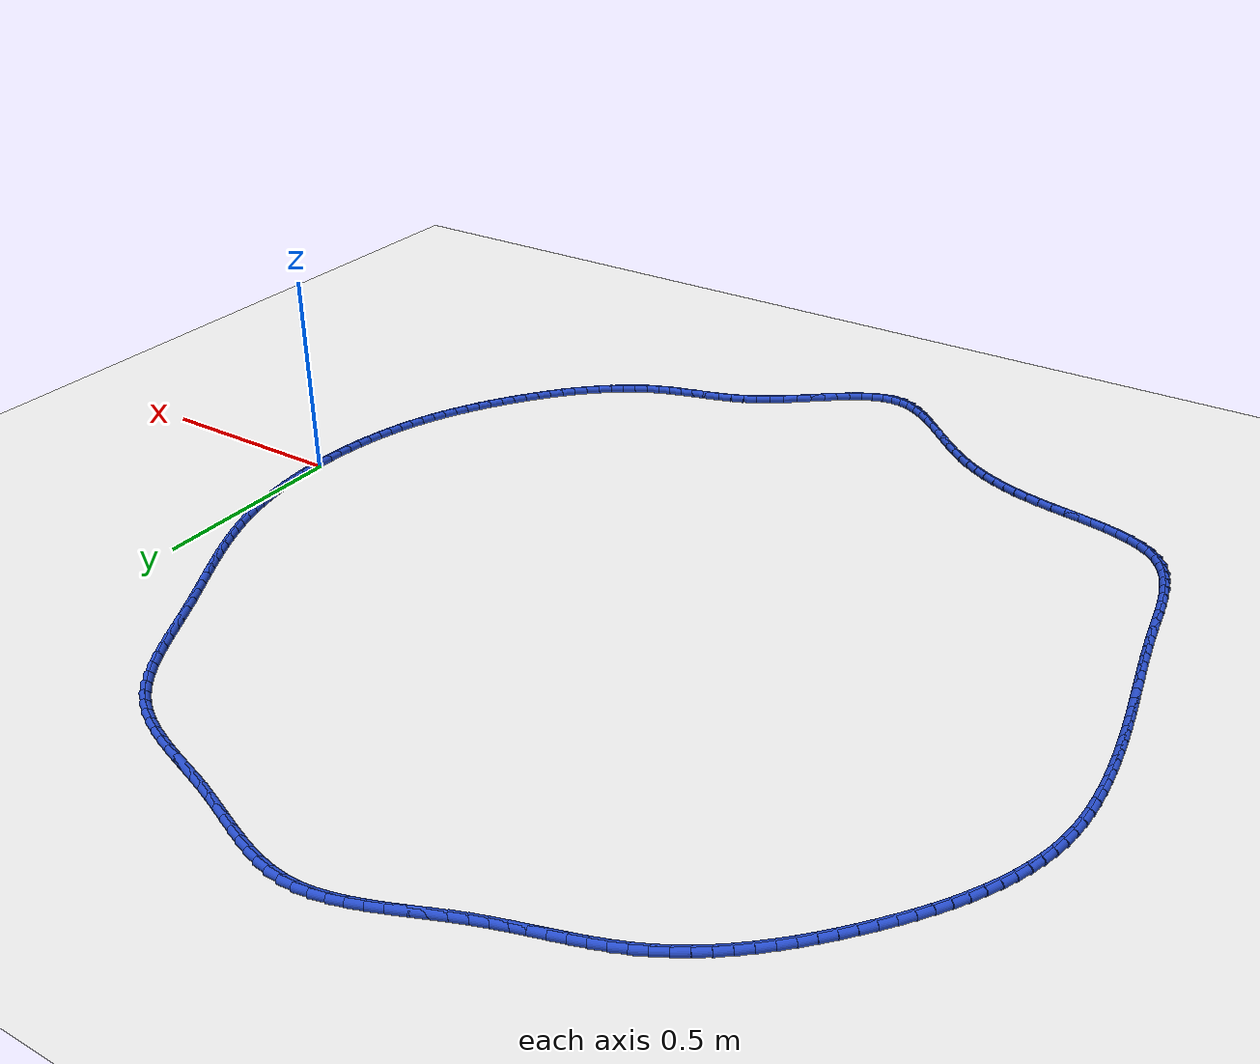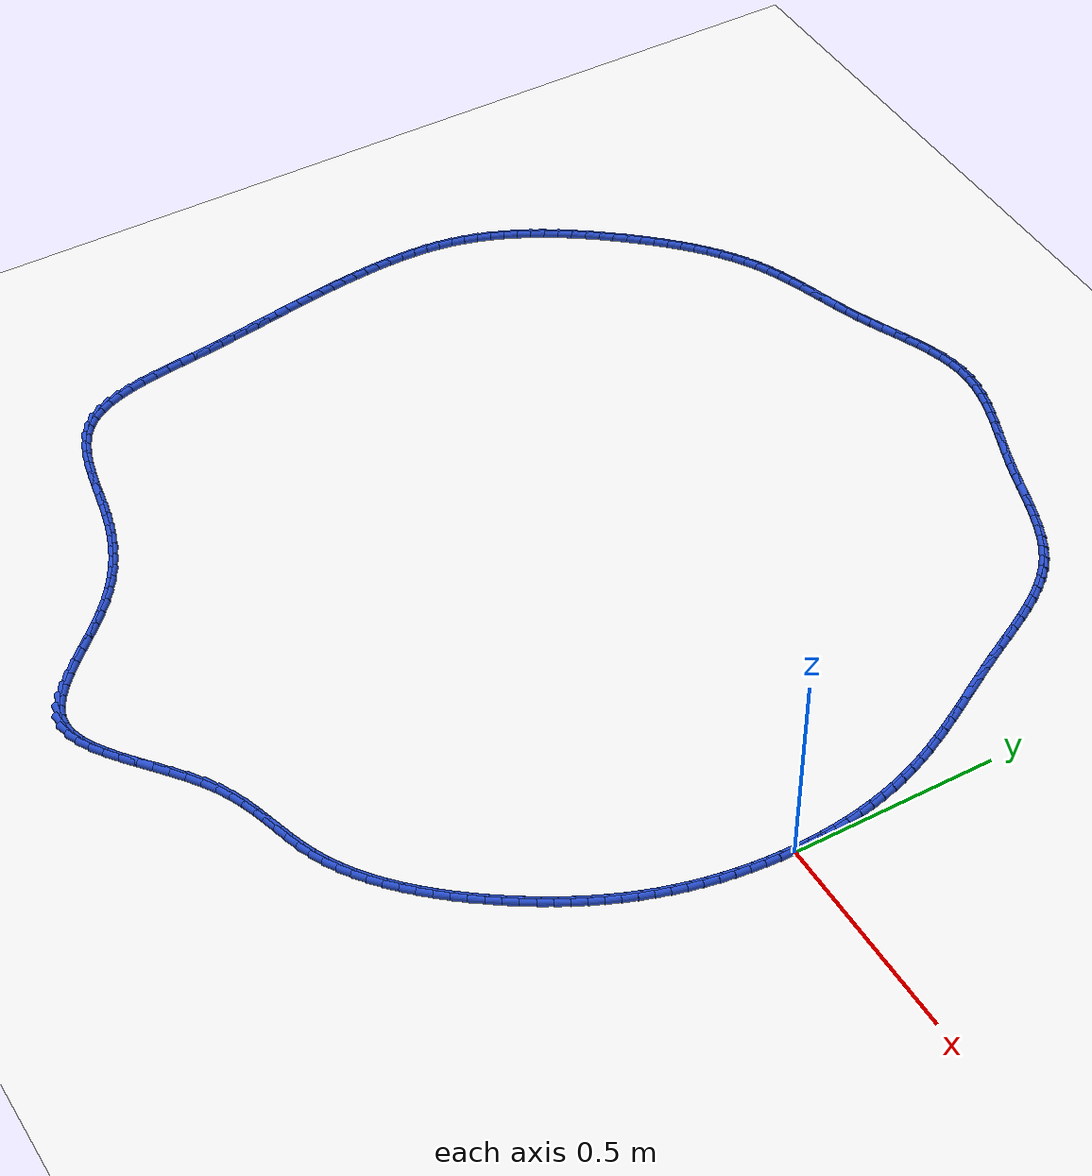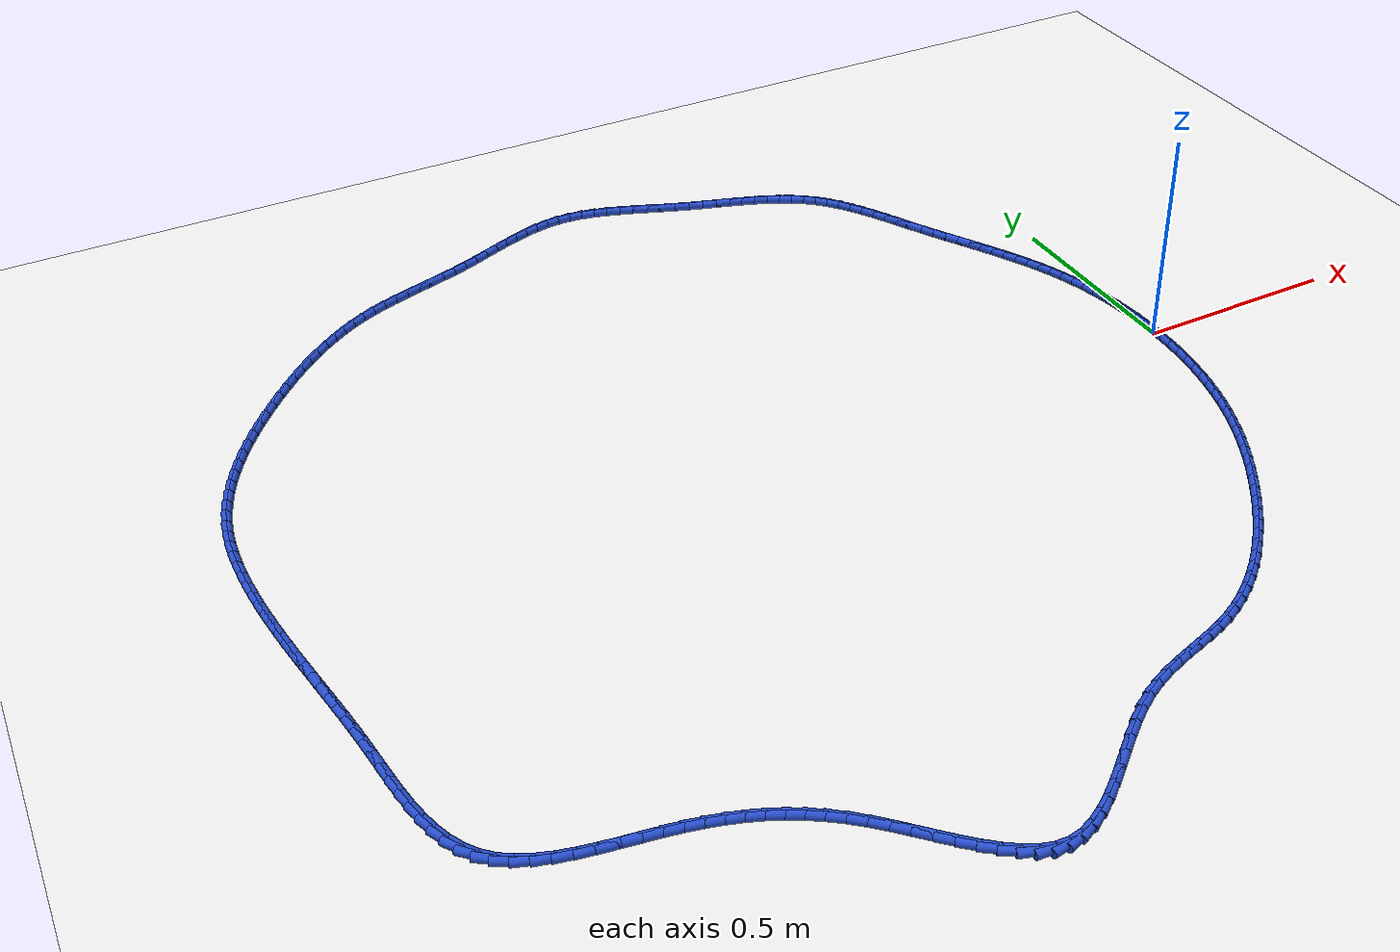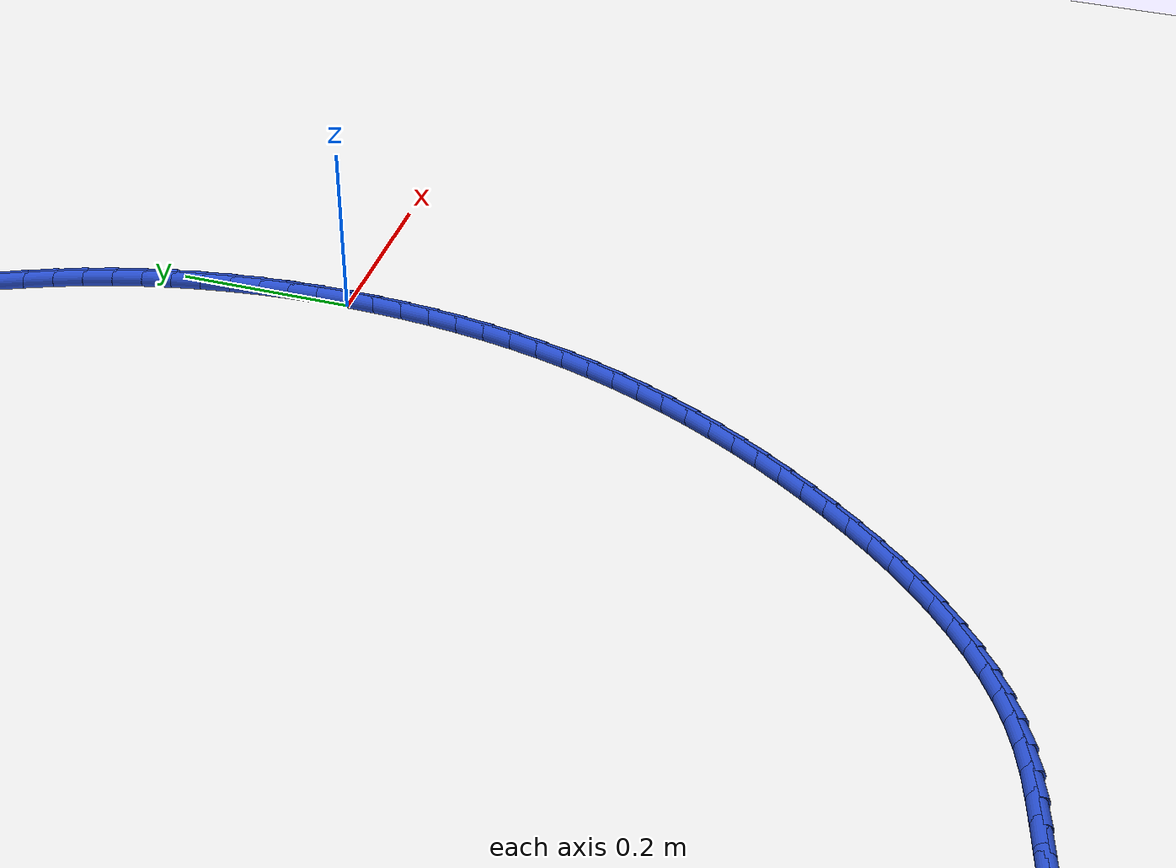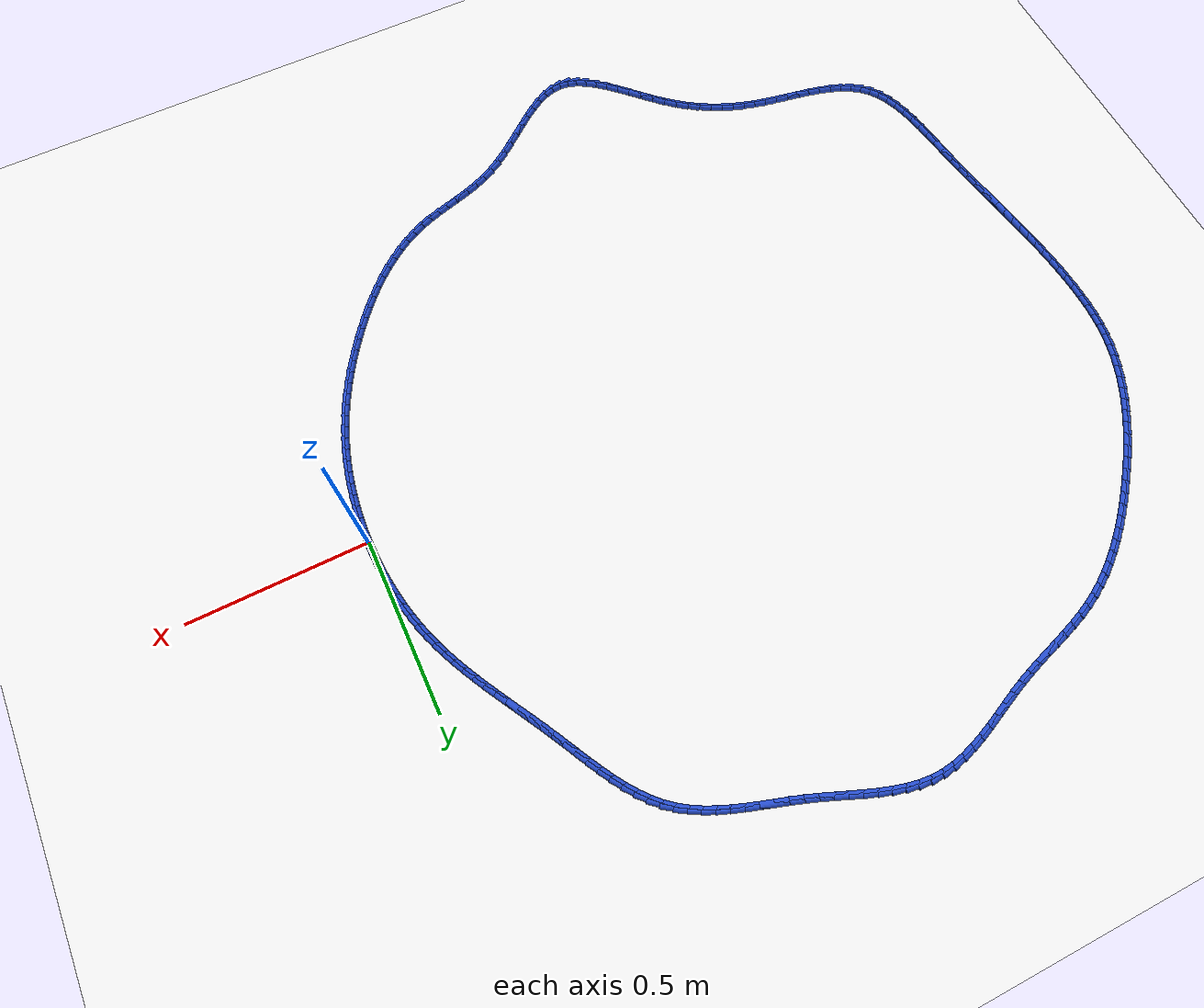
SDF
<sdf version="1.6">
 <world name="default">
  <light name="sun" type="directional">
   <pose>0 0 10 0 -0 0</pose>
   <diffuse>0.8 0.8 0.8 1</diffuse>
   <specular>0.2 0.2 0.2 1</specular>
   <attenuation>
    <range>1000</range>
    <constant>0.9</constant>
    <linear>0.01</linear>
    <quadratic>0.001</quadratic>
   </attenuation>
   <direction>-0.5 0.1 -0.9</direction>
  </light>
  <model name="ground_plane">
   <static>1</static>
   <link name="link">
    <collision name="collision">
     <geometry><plane><normal>0 0 1</normal><size>100 100</size></plane></geometry>
     <surface><friction><ode><mu>100</mu><mu2>50</mu2></ode></friction></surface>
    </collision>
    <visual name="visual">
     <cast_shadows>0</cast_shadows>
     <geometry><plane><normal>0 0 1</normal><size>100 100</size></plane></geometry>
     <material>
      <script><uri>file://media/materials/scripts/gazebo.material</uri><name>Gazebo/WhiteGlow</name></script>
     </material>
    </visual>
   </link>
  </model>
  <gravity>0 0 -9.8</gravity>
  <magnetic_field>6e-06 2.3e-05 -4.2e-05</magnetic_field>
  <atmosphere type="adiabatic"/>
  <physics name="default_physics" default="0" type="ode">
   <max_step_size>0.001</max_step_size>
   <real_time_factor>1</real_time_factor>
   <real_time_update_rate>1000</real_time_update_rate>
  </physics>
  <scene><ambient>0.4 0.4 0.4 1</ambient><background>0.7 0.7 0.7 1</background><shadows>1</shadows></scene>
  <spherical_coordinates>
   <surface_model>EARTH_WGS84</surface_model>
   <latitude_deg>0</latitude_deg>
   <longitude_deg>0</longitude_deg>
   <elevation>0</elevation>
   <heading_deg>0</heading_deg>
  </spherical_coordinates>
  <model name="line">
   <link name="link_0">
    <pose>-1.5612511283791264e-17 6.938893903907228e-18 0.01 0 1.57 -1.5566706766583696</pose>
    <collision name="collision">
     <geometry><cylinder><radius>0.01</radius><length>0.08</length></cylinder></geometry>
    </collision>
    <visual name="visual">
     <material>
      <script><name>Gazebo/Blue</name><uri>file://media/materials/scripts/gazebo.material</uri></script>
     </material>
     <geometry><cylinder><radius>0.01</radius><length>0.08</length></cylinder></geometry>
    </visual>
   </link>
   <link name="link_1">
    <pose>-0.0004900673434367412 0.0346911287789064 0.01 0 1.57 -1.523045920425543</pose>
    <collision name="collision">
     <geometry><cylinder><radius>0.01</radius><length>0.08</length></cylinder></geometry>
    </collision>
    <visual name="visual">
     <material>
      <script><name>Gazebo/Blue</name><uri>file://media/materials/scripts/gazebo.material</uri></script>
     </material>
     <geometry><cylinder><radius>0.01</radius><length>0.08</length></cylinder></geometry>
    </visual>
   </link>
   <link name="link_2">
    <pose>-0.002146241075896673 0.06934873525694304 0.01 0 1.57 -1.48888646400225</pose>
    <collision name="collision">
     <geometry><cylinder><radius>0.01</radius><length>0.08</length></cylinder></geometry>
    </collision>
    <visual name="visual">
     <material>
      <script><name>Gazebo/Blue</name><uri>file://media/materials/scripts/gazebo.material</uri></script>
     </material>
     <geometry><cylinder><radius>0.01</radius><length>0.08</length></cylinder></geometry>
    </visual>
   </link>
   <link name="link_3">
    <pose>-0.004982825967281971 0.10390181827954102 0.01 0 1.57 -1.4540639703913751</pose>
    <collision name="collision">
     <geometry><cylinder><radius>0.01</radius><length>0.08</length></cylinder></geometry>
    </collision>
    <visual name="visual">
     <material>
      <script><name>Gazebo/Blue</name><uri>file://media/materials/scripts/gazebo.material</uri></script>
     </material>
     <geometry><cylinder><radius>0.01</radius><length>0.08</length></cylinder></geometry>
    </visual>
   </link>
   <link name="link_4">
    <pose>-0.009014126787494792 0.13827937669213156 0.01 0 1.57 -1.4184505879691864</pose>
    <collision name="collision">
     <geometry><cylinder><radius>0.01</radius><length>0.08</length></cylinder></geometry>
    </collision>
    <visual name="visual">
     <material>
      <script><name>Gazebo/Blue</name><uri>file://media/materials/scripts/gazebo.material</uri></script>
     </material>
     <geometry><cylinder><radius>0.01</radius><length>0.08</length></cylinder></geometry>
    </visual>
   </link>
   <link name="link_5">
    <pose>-0.014254448306437292 0.17241040934014565 0.01 0 1.57 -1.381919109163995</pose>
    <collision name="collision">
     <geometry><cylinder><radius>0.01</radius><length>0.08</length></cylinder></geometry>
    </collision>
    <visual name="visual">
     <material>
      <script><name>Gazebo/Blue</name><uri>file://media/materials/scripts/gazebo.material</uri></script>
     </material>
     <geometry><cylinder><radius>0.01</radius><length>0.08</length></cylinder></geometry>
    </visual>
   </link>
   <link name="link_6">
    <pose>-0.02071809529401163 0.2062239150690146 0.01 0 1.57 -1.3443434558938452</pose>
    <collision name="collision">
     <geometry><cylinder><radius>0.01</radius><length>0.08</length></cylinder></geometry>
    </collision>
    <visual name="visual">
     <material>
      <script><name>Gazebo/Blue</name><uri>file://media/materials/scripts/gazebo.material</uri></script>
     </material>
     <geometry><cylinder><radius>0.01</radius><length>0.08</length></cylinder></geometry>
    </visual>
   </link>
   <link name="link_7">
    <pose>-0.02841937252011996 0.23964889272416934 0.01 0 1.57 -1.3055995590511331</pose>
    <collision name="collision">
     <geometry><cylinder><radius>0.01</radius><length>0.08</length></cylinder></geometry>
    </collision>
    <visual name="visual">
     <material>
      <script><name>Gazebo/Blue</name><uri>file://media/materials/scripts/gazebo.material</uri></script>
     </material>
     <geometry><cylinder><radius>0.01</radius><length>0.08</length></cylinder></geometry>
    </visual>
   </link>
   <link name="link_8">
    <pose>-0.03737258475466444 0.27261434115104116 0.01 0 1.57 -1.265566706927805</pose>
    <collision name="collision">
     <geometry><cylinder><radius>0.01</radius><length>0.08</length></cylinder></geometry>
    </collision>
    <visual name="visual">
     <material>
      <script><name>Gazebo/Blue</name><uri>file://media/materials/scripts/gazebo.material</uri></script>
     </material>
     <geometry><cylinder><radius>0.01</radius><length>0.08</length></cylinder></geometry>
    </visual>
   </link>
   <link name="link_9">
    <pose>-0.047592036767547224 0.30504925919506104 0.01 0 1.57 -1.2247759609433497</pose>
    <collision name="collision">
     <geometry><cylinder><radius>0.01</radius><length>0.08</length></cylinder></geometry>
    </collision>
    <visual name="visual">
     <material>
      <script><name>Gazebo/Blue</name><uri>file://media/materials/scripts/gazebo.material</uri></script>
     </material>
     <geometry><cylinder><radius>0.01</radius><length>0.08</length></cylinder></geometry>
    </visual>
   </link>
   <link name="link_10">
    <pose>-0.05907532485397768 0.3369008217877752 0.01 0 1.57 -1.1870147176725165</pose>
    <collision name="collision">
     <geometry><cylinder><radius>0.01</radius><length>0.08</length></cylinder></geometry>
    </collision>
    <visual name="visual">
     <material>
      <script><name>Gazebo/Blue</name><uri>file://media/materials/scripts/gazebo.material</uri></script>
     </material>
     <geometry><cylinder><radius>0.01</radius><length>0.08</length></cylinder></geometry>
    </visual>
   </link>
   <link name="link_11">
    <pose>-0.07172290182622323 0.368221880072586 0.01 0 1.57 -1.1538654905790988</pose>
    <collision name="collision">
     <geometry><cylinder><radius>0.01</radius><length>0.08</length></cylinder></geometry>
    </collision>
    <visual name="visual">
     <material>
      <script><name>Gazebo/Blue</name><uri>file://media/materials/scripts/gazebo.material</uri></script>
     </material>
     <geometry><cylinder><radius>0.01</radius><length>0.08</length></cylinder></geometry>
    </visual>
   </link>
   <link name="link_12">
    <pose>-0.08540020388333962 0.3991033775375834 0.01 0 1.57 -1.1254984513892936</pose>
    <collision name="collision">
     <geometry><cylinder><radius>0.01</radius><length>0.08</length></cylinder></geometry>
    </collision>
    <visual name="visual">
     <material>
      <script><name>Gazebo/Blue</name><uri>file://media/materials/scripts/gazebo.material</uri></script>
     </material>
     <geometry><cylinder><radius>0.01</radius><length>0.08</length></cylinder></geometry>
    </visual>
   </link>
   <link name="link_13">
    <pose>-0.09997262039151786 0.429636308617349 0.01 0 1.57 -1.1020029698760332</pose>
    <collision name="collision">
     <geometry><cylinder><radius>0.01</radius><length>0.08</length></cylinder></geometry>
    </collision>
    <visual name="visual">
     <material>
      <script><name>Gazebo/Blue</name><uri>file://media/materials/scripts/gazebo.material</uri></script>
     </material>
     <geometry><cylinder><radius>0.01</radius><length>0.08</length></cylinder></geometry>
    </visual>
   </link>
   <link name="link_14">
    <pose>-0.11530554071694896 0.4599116677464648 0.01 0 1.57 -1.083407689069498</pose>
    <collision name="collision">
     <geometry><cylinder><radius>0.01</radius><length>0.08</length></cylinder></geometry>
    </collision>
    <visual name="visual">
     <material>
      <script><name>Gazebo/Blue</name><uri>file://media/materials/scripts/gazebo.material</uri></script>
     </material>
     <geometry><cylinder><radius>0.01</radius><length>0.08</length></cylinder></geometry>
    </visual>
   </link>
   <link name="link_15">
    <pose>-0.13126435422582394 0.4900204493595128 0.01 0 1.57 -1.0696972753918943</pose>
    <collision name="collision">
     <geometry><cylinder><radius>0.01</radius><length>0.08</length></cylinder></geometry>
    </collision>
    <visual name="visual">
     <material>
      <script><name>Gazebo/Blue</name><uri>file://media/materials/scripts/gazebo.material</uri></script>
     </material>
     <geometry><cylinder><radius>0.01</radius><length>0.08</length></cylinder></geometry>
    </visual>
   </link>
   <link name="link_16">
    <pose>-0.147714450284334 0.5200536478910751 0.01 0 1.57 -1.0608263361486272</pose>
    <collision name="collision">
     <geometry><cylinder><radius>0.01</radius><length>0.08</length></cylinder></geometry>
    </collision>
    <visual name="visual">
     <material>
      <script><name>Gazebo/Blue</name><uri>file://media/materials/scripts/gazebo.material</uri></script>
     </material>
     <geometry><cylinder><radius>0.01</radius><length>0.08</length></cylinder></geometry>
    </visual>
   </link>
   <link name="link_17">
    <pose>-0.16452121825867005 0.5501022577757335 0.01 0 1.57 -1.0567298813475996</pose>
    <collision name="collision">
     <geometry><cylinder><radius>0.01</radius><length>0.08</length></cylinder></geometry>
    </collision>
    <visual name="visual">
     <material>
      <script><name>Gazebo/Blue</name><uri>file://media/materials/scripts/gazebo.material</uri></script>
     </material>
     <geometry><cylinder><radius>0.01</radius><length>0.08</length></cylinder></geometry>
    </visual>
   </link>
   <link name="link_18">
    <pose>-0.1815500475150231 0.5802572734480698 0.01 0 1.57 -1.057330188167922</pose>
    <collision name="collision">
     <geometry><cylinder><radius>0.01</radius><length>0.08</length></cylinder></geometry>
    </collision>
    <visual name="visual">
     <material>
      <script><name>Gazebo/Blue</name><uri>file://media/materials/scripts/gazebo.material</uri></script>
     </material>
     <geometry><cylinder><radius>0.01</radius><length>0.08</length></cylinder></geometry>
    </visual>
   </link>
   <link name="link_19">
    <pose>-0.1986663274195844 0.6106096893426662 0.01 0 1.57 -1.0625402167533928</pose>
    <collision name="collision">
     <geometry><cylinder><radius>0.01</radius><length>0.08</length></cylinder></geometry>
    </collision>
    <visual name="visual">
     <material>
      <script><name>Gazebo/Blue</name><uri>file://media/materials/scripts/gazebo.material</uri></script>
     </material>
     <geometry><cylinder><radius>0.01</radius><length>0.08</length></cylinder></geometry>
    </visual>
   </link>
   <link name="link_20">
    <pose>-0.2157354473385448 0.6412504998941044 0.01 0 1.57 -1.0722638826018733</pose>
    <collision name="collision">
     <geometry><cylinder><radius>0.01</radius><length>0.08</length></cylinder></geometry>
    </collision>
    <visual name="visual">
     <material>
      <script><name>Gazebo/Blue</name><uri>file://media/materials/scripts/gazebo.material</uri></script>
     </material>
     <geometry><cylinder><radius>0.01</radius><length>0.08</length></cylinder></geometry>
    </visual>
   </link>
   <link name="link_21">
    <pose>-0.23262279663809535 0.6722706995369664 0.01 0 1.57 -1.0849985773672532</pose>
    <collision name="collision">
     <geometry><cylinder><radius>0.01</radius><length>0.08</length></cylinder></geometry>
    </collision>
    <visual name="visual">
     <material>
      <script><name>Gazebo/Blue</name><uri>file://media/materials/scripts/gazebo.material</uri></script>
     </material>
     <geometry><cylinder><radius>0.01</radius><length>0.08</length></cylinder></geometry>
    </visual>
   </link>
   <link name="link_22">
    <pose>-0.24922937588767127 0.7037224121885397 0.01 0 1.57 -1.0908803957089008</pose>
    <collision name="collision">
     <geometry><cylinder><radius>0.01</radius><length>0.08</length></cylinder></geometry>
    </collision>
    <visual name="visual">
     <material>
      <script><name>Gazebo/Blue</name><uri>file://media/materials/scripts/gazebo.material</uri></script>
     </material>
     <geometry><cylinder><radius>0.01</radius><length>0.08</length></cylinder></geometry>
    </visual>
   </link>
   <link name="link_23">
    <pose>-0.26570850143330266 0.7353823527974587 0.01 0 1.57 -1.08578803404934</pose>
    <collision name="collision">
     <geometry><cylinder><radius>0.01</radius><length>0.08</length></cylinder></geometry>
    </collision>
    <visual name="visual">
     <material>
      <script><name>Gazebo/Blue</name><uri>file://media/materials/scripts/gazebo.material</uri></script>
     </material>
     <geometry><cylinder><radius>0.01</radius><length>0.08</length></cylinder></geometry>
    </visual>
   </link>
   <link name="link_24">
    <pose>-0.28232245939871015 0.7669082930798221 0.01 0 1.57 -1.0695760120328102</pose>
    <collision name="collision">
     <geometry><cylinder><radius>0.01</radius><length>0.08</length></cylinder></geometry>
    </collision>
    <visual name="visual">
     <material>
      <script><name>Gazebo/Blue</name><uri>file://media/materials/scripts/gazebo.material</uri></script>
     </material>
     <geometry><cylinder><radius>0.01</radius><length>0.08</length></cylinder></geometry>
    </visual>
   </link>
   <link name="link_25">
    <pose>-0.2993339675715128 0.7979575335798095 0.01 0 1.57 -1.0417918439166296</pose>
    <collision name="collision">
     <geometry><cylinder><radius>0.01</radius><length>0.08</length></cylinder></geometry>
    </collision>
    <visual name="visual">
     <material>
      <script><name>Gazebo/Blue</name><uri>file://media/materials/scripts/gazebo.material</uri></script>
     </material>
     <geometry><cylinder><radius>0.01</radius><length>0.08</length></cylinder></geometry>
    </visual>
   </link>
   <link name="link_26">
    <pose>-0.3170057437393292 0.8281873748415989 0.01 0 1.57 -1.001692889915784</pose>
    <collision name="collision">
     <geometry><cylinder><radius>0.01</radius><length>0.08</length></cylinder></geometry>
    </collision>
    <visual name="visual">
     <material>
      <script><name>Gazebo/Blue</name><uri>file://media/materials/scripts/gazebo.material</uri></script>
     </material>
     <geometry><cylinder><radius>0.01</radius><length>0.08</length></cylinder></geometry>
    </visual>
   </link>
   <link name="link_27">
    <pose>-0.3356005056897782 0.857255117409369 0.01 0 1.57 -0.9483246335831264</pose>
    <collision name="collision">
     <geometry><cylinder><radius>0.01</radius><length>0.08</length></cylinder></geometry>
    </collision>
    <visual name="visual">
     <material>
      <script><name>Gazebo/Blue</name><uri>file://media/materials/scripts/gazebo.material</uri></script>
     </material>
     <geometry><cylinder><radius>0.01</radius><length>0.08</length></cylinder></geometry>
    </visual>
   </link>
   <link name="link_28">
    <pose>-0.3553809712104785 0.8848180618272989 0.01 0 1.57 -0.8806806798011156</pose>
    <collision name="collision">
     <geometry><cylinder><radius>0.01</radius><length>0.08</length></cylinder></geometry>
    </collision>
    <visual name="visual">
     <material>
      <script><name>Gazebo/Blue</name><uri>file://media/materials/scripts/gazebo.material</uri></script>
     </material>
     <geometry><cylinder><radius>0.01</radius><length>0.08</length></cylinder></geometry>
    </visual>
   </link>
   <link name="link_29">
    <pose>-0.37660985808904895 0.9105335086395672 0.01 0 1.57 -0.7979923592808547</pose>
    <collision name="collision">
     <geometry><cylinder><radius>0.01</radius><length>0.08</length></cylinder></geometry>
    </collision>
    <visual name="visual">
     <material>
      <script><name>Gazebo/Blue</name><uri>file://media/materials/scripts/gazebo.material</uri></script>
     </material>
     <geometry><cylinder><radius>0.01</radius><length>0.08</length></cylinder></geometry>
    </visual>
   </link>
   <link name="link_30">
    <pose>-0.3995498841131082 0.9340587583903524 0.01 0 1.57 -0.7005278589553152</pose>
    <collision name="collision">
     <geometry><cylinder><radius>0.01</radius><length>0.08</length></cylinder></geometry>
    </collision>
    <visual name="visual">
     <material>
      <script><name>Gazebo/Blue</name><uri>file://media/materials/scripts/gazebo.material</uri></script>
     </material>
     <geometry><cylinder><radius>0.01</radius><length>0.08</length></cylinder></geometry>
    </visual>
   </link>
   <link name="link_31">
    <pose>-0.4244572214693882 0.9550604043275415 0.01 0 1.57 -0.6012012309865363</pose>
    <collision name="collision">
     <geometry><cylinder><radius>0.01</radius><length>0.08</length></cylinder></geometry>
    </collision>
    <visual name="visual">
     <material>
      <script><name>Gazebo/Blue</name><uri>file://media/materials/scripts/gazebo.material</uri></script>
     </material>
     <geometry><cylinder><radius>0.01</radius><length>0.08</length></cylinder></geometry>
    </visual>
   </link>
   <link name="link_32">
    <pose>-0.45136746682825757 0.9735181878658834 0.01 0 1.57 -0.5161398221864067</pose>
    <collision name="collision">
     <geometry><cylinder><radius>0.01</radius><length>0.08</length></cylinder></geometry>
    </collision>
    <visual name="visual">
     <material>
      <script><name>Gazebo/Blue</name><uri>file://media/materials/scripts/gazebo.material</uri></script>
     </material>
     <geometry><cylinder><radius>0.01</radius><length>0.08</length></cylinder></geometry>
    </visual>
   </link>
   <link name="link_33">
    <pose>-0.48004787459840714 0.9897928124086621 0.01 0 1.57 -0.4469389475374719</pose>
    <collision name="collision">
     <geometry><cylinder><radius>0.01</radius><length>0.08</length></cylinder></geometry>
    </collision>
    <visual name="visual">
     <material>
      <script><name>Gazebo/Blue</name><uri>file://media/materials/scripts/gazebo.material</uri></script>
     </material>
     <geometry><cylinder><radius>0.01</radius><length>0.08</length></cylinder></geometry>
    </visual>
   </link>
   <link name="link_34">
    <pose>-0.5102494850173985 1.0042680004052036 0.01 0 1.57 -0.3933112020701655</pose>
    <collision name="collision">
     <geometry><cylinder><radius>0.01</radius><length>0.08</length></cylinder></geometry>
    </collision>
    <visual name="visual">
     <material>
      <script><name>Gazebo/Blue</name><uri>file://media/materials/scripts/gazebo.material</uri></script>
     </material>
     <geometry><cylinder><radius>0.01</radius><length>0.08</length></cylinder></geometry>
    </visual>
   </link>
   <link name="link_35">
    <pose>-0.5417233383227925 1.017327474304832 0.01 0 1.57 -0.3544757792458659</pose>
    <collision name="collision">
     <geometry><cylinder><radius>0.01</radius><length>0.08</length></cylinder></geometry>
    </collision>
    <visual name="visual">
     <material>
      <script><name>Gazebo/Blue</name><uri>file://media/materials/scripts/gazebo.material</uri></script>
     </material>
     <geometry><cylinder><radius>0.01</radius><length>0.08</length></cylinder></geometry>
    </visual>
   </link>
   <link name="link_36">
    <pose>-0.5742204747521503 1.0293549565568727 0.01 0 1.57 -0.3295402285301992</pose>
    <collision name="collision">
     <geometry><cylinder><radius>0.01</radius><length>0.08</length></cylinder></geometry>
    </collision>
    <visual name="visual">
     <material>
      <script><name>Gazebo/Blue</name><uri>file://media/materials/scripts/gazebo.material</uri></script>
     </material>
     <geometry><cylinder><radius>0.01</radius><length>0.08</length></cylinder></geometry>
    </visual>
   </link>
   <link name="link_37">
    <pose>-0.6074919345430333 1.040734169610651 0.01 0 1.57 -0.3177256534506979</pose>
    <collision name="collision">
     <geometry><cylinder><radius>0.01</radius><length>0.08</length></cylinder></geometry>
    </collision>
    <visual name="visual">
     <material>
      <script><name>Gazebo/Blue</name><uri>file://media/materials/scripts/gazebo.material</uri></script>
     </material>
     <geometry><cylinder><radius>0.01</radius><length>0.08</length></cylinder></geometry>
    </visual>
   </link>
   <link name="link_38">
    <pose>-0.6412887579330023 1.0518488359154907 0.01 0 1.57 -0.3184743240165572</pose>
    <collision name="collision">
     <geometry><cylinder><radius>0.01</radius><length>0.08</length></cylinder></geometry>
    </collision>
    <visual name="visual">
     <material>
      <script><name>Gazebo/Blue</name><uri>file://media/materials/scripts/gazebo.material</uri></script>
     </material>
     <geometry><cylinder><radius>0.01</radius><length>0.08</length></cylinder></geometry>
    </visual>
   </link>
   <link name="link_39">
    <pose>-0.6753619851596188 1.0630826779207183 0.01 0 1.57 -0.3314798272515674</pose>
    <collision name="collision">
     <geometry><cylinder><radius>0.01</radius><length>0.08</length></cylinder></geometry>
    </collision>
    <visual name="visual">
     <material>
      <script><name>Gazebo/Blue</name><uri>file://media/materials/scripts/gazebo.material</uri></script>
     </material>
     <geometry><cylinder><radius>0.01</radius><length>0.08</length></cylinder></geometry>
    </visual>
   </link>
   <link name="link_40">
    <pose>-0.7094626564604437 1.0748194180756578 0.01 0 1.57 -0.35572074002398557</pose>
    <collision name="collision">
     <geometry><cylinder><radius>0.01</radius><length>0.08</length></cylinder></geometry>
    </collision>
    <visual name="visual">
     <material>
      <script><name>Gazebo/Blue</name><uri>file://media/materials/scripts/gazebo.material</uri></script>
     </material>
     <geometry><cylinder><radius>0.01</radius><length>0.08</length></cylinder></geometry>
    </visual>
   </link>
   <link name="link_41">
    <pose>-0.7433518754834928 1.0874101148099824 0.01 0 1.57 -0.3771212548321683</pose>
    <collision name="collision">
     <geometry><cylinder><radius>0.01</radius><length>0.08</length></cylinder></geometry>
    </collision>
    <visual name="visual">
     <material>
      <script><name>Gazebo/Blue</name><uri>file://media/materials/scripts/gazebo.material</uri></script>
     </material>
     <geometry><cylinder><radius>0.01</radius><length>0.08</length></cylinder></geometry>
    </visual>
   </link>
   <link name="link_42">
    <pose>-0.7769421208601217 1.100714490593918 0.01 0 1.57 -0.3848954030329804</pose>
    <collision name="collision">
     <geometry><cylinder><radius>0.01</radius><length>0.08</length></cylinder></geometry>
    </collision>
    <visual name="visual">
     <material>
      <script><name>Gazebo/Blue</name><uri>file://media/materials/scripts/gazebo.material</uri></script>
     </material>
     <geometry><cylinder><radius>0.01</radius><length>0.08</length></cylinder></geometry>
    </visual>
   </link>
   <link name="link_43">
    <pose>-0.8102628087235578 1.1142127098068642 0.01 0 1.57 -0.37865377219817575</pose>
    <collision name="collision">
     <geometry><cylinder><radius>0.01</radius><length>0.08</length></cylinder></geometry>
    </collision>
    <visual name="visual">
     <material>
      <script><name>Gazebo/Blue</name><uri>file://media/materials/scripts/gazebo.material</uri></script>
     </material>
     <geometry><cylinder><radius>0.01</radius><length>0.08</length></cylinder></geometry>
    </visual>
   </link>
   <link name="link_44">
    <pose>-0.843346386950068 1.1273750963358018 0.01 0 1.57 -0.35789801835958807</pose>
    <collision name="collision">
     <geometry><cylinder><radius>0.01</radius><length>0.08</length></cylinder></geometry>
    </collision>
    <visual name="visual">
     <material>
      <script><name>Gazebo/Blue</name><uri>file://media/materials/scripts/gazebo.material</uri></script>
     </material>
     <geometry><cylinder><radius>0.01</radius><length>0.08</length></cylinder></geometry>
    </visual>
   </link>
   <link name="link_45">
    <pose>-0.8762253034159193 1.139671974067712 0.01 0 1.57 -0.3217356572306002</pose>
    <collision name="collision">
     <geometry><cylinder><radius>0.01</radius><length>0.08</length></cylinder></geometry>
    </collision>
    <visual name="visual">
     <material>
      <script><name>Gazebo/Blue</name><uri>file://media/materials/scripts/gazebo.material</uri></script>
     </material>
     <geometry><cylinder><radius>0.01</radius><length>0.08</length></cylinder></geometry>
    </visual>
   </link>
   <link name="link_46">
    <pose>-0.9089320059973791 1.1505736668895767 0.01 0 1.57 -0.2689634394208477</pose>
    <collision name="collision">
     <geometry><cylinder><radius>0.01</radius><length>0.08</length></cylinder></geometry>
    </collision>
    <visual name="visual">
     <material>
      <script><name>Gazebo/Blue</name><uri>file://media/materials/scripts/gazebo.material</uri></script>
     </material>
     <geometry><cylinder><radius>0.01</radius><length>0.08</length></cylinder></geometry>
    </visual>
   </link>
   <link name="link_47">
    <pose>-0.9414989425707143 1.1595504986883767 0.01 0 1.57 -0.19829506514048606</pose>
    <collision name="collision">
     <geometry><cylinder><radius>0.01</radius><length>0.08</length></cylinder></geometry>
    </collision>
    <visual name="visual">
     <material>
      <script><name>Gazebo/Blue</name><uri>file://media/materials/scripts/gazebo.material</uri></script>
     </material>
     <geometry><cylinder><radius>0.01</radius><length>0.08</length></cylinder></geometry>
    </visual>
   </link>
   <link name="link_48">
    <pose>-0.973958561012192 1.1660727933510937 0.01 0 1.57 -0.10881988776421461</pose>
    <collision name="collision">
     <geometry><cylinder><radius>0.01</radius><length>0.08</length></cylinder></geometry>
    </collision>
    <visual name="visual">
     <material>
      <script><name>Gazebo/Blue</name><uri>file://media/materials/scripts/gazebo.material</uri></script>
     </material>
     <geometry><cylinder><radius>0.01</radius><length>0.08</length></cylinder></geometry>
    </visual>
   </link>
   <link name="link_49">
    <pose>-1.0063433091980798 1.1696108747647087 0.01 0 1.57 -0.000877059354770341</pose>
    <collision name="collision">
     <geometry><cylinder><radius>0.01</radius><length>0.08</length></cylinder></geometry>
    </collision>
    <visual name="visual">
     <material>
      <script><name>Gazebo/Blue</name><uri>file://media/materials/scripts/gazebo.material</uri></script>
     </material>
     <geometry><cylinder><radius>0.01</radius><length>0.08</length></cylinder></geometry>
    </visual>
   </link>
   <link name="link_50">
    <pose>-1.0386855855951531 1.1696392408680507 0.01 0 1.57 0.1121058892237755</pose>
    <collision name="collision">
     <geometry><cylinder><radius>0.01</radius><length>0.08</length></cylinder></geometry>
    </collision>
    <visual name="visual">
     <material>
      <script><name>Gazebo/Blue</name><uri>file://media/materials/scripts/gazebo.material</uri></script>
     </material>
     <geometry><cylinder><radius>0.01</radius><length>0.08</length></cylinder></geometry>
    </visual>
   </link>
   <link name="link_51">
    <pose>-1.0710134390627517 1.1659998389783468 0.01 0 1.57 0.20775080116748892</pose>
    <collision name="collision">
     <geometry><cylinder><radius>0.01</radius><length>0.08</length></cylinder></geometry>
    </collision>
    <visual name="visual">
     <material>
      <script><name>Gazebo/Blue</name><uri>file://media/materials/scripts/gazebo.material</uri></script>
     </material>
     <geometry><cylinder><radius>0.01</radius><length>0.08</length></cylinder></geometry>
    </visual>
   </link>
   <link name="link_52">
    <pose>-1.1033472299933533 1.1591841284460362 0.01 0 1.57 0.28368129305164086</pose>
    <collision name="collision">
     <geometry><cylinder><radius>0.01</radius><length>0.08</length></cylinder></geometry>
    </collision>
    <visual name="visual">
     <material>
      <script><name>Gazebo/Blue</name><uri>file://media/materials/scripts/gazebo.material</uri></script>
     </material>
     <geometry><cylinder><radius>0.01</radius><length>0.08</length></cylinder></geometry>
    </visual>
   </link>
   <link name="link_53">
    <pose>-1.1357065328907086 1.1497499595151255 0.01 0 1.57 0.34088152159653085</pose>
    <collision name="collision">
     <geometry><cylinder><radius>0.01</radius><length>0.08</length></cylinder></geometry>
    </collision>
    <visual name="visual">
     <material>
      <script><name>Gazebo/Blue</name><uri>file://media/materials/scripts/gazebo.material</uri></script>
     </material>
     <geometry><cylinder><radius>0.01</radius><length>0.08</length></cylinder></geometry>
    </visual>
   </link>
   <link name="link_54">
    <pose>-1.1681109222585675 1.1382551824296203 0.01 0 1.57 0.38076959369098706</pose>
    <collision name="collision">
     <geometry><cylinder><radius>0.01</radius><length>0.08</length></cylinder></geometry>
    </collision>
    <visual name="visual">
     <material>
      <script><name>Gazebo/Blue</name><uri>file://media/materials/scripts/gazebo.material</uri></script>
     </material>
     <geometry><cylinder><radius>0.01</radius><length>0.08</length></cylinder></geometry>
    </visual>
   </link>
   <link name="link_55">
    <pose>-1.2005799726006814 1.1252576474335267 0.01 0 1.57 0.4046590879387723</pose>
    <collision name="collision">
     <geometry><cylinder><radius>0.01</radius><length>0.08</length></cylinder></geometry>
    </collision>
    <visual name="visual">
     <material>
      <script><name>Gazebo/Blue</name><uri>file://media/materials/scripts/gazebo.material</uri></script>
     </material>
     <geometry><cylinder><radius>0.01</radius><length>0.08</length></cylinder></geometry>
    </visual>
   </link>
   <link name="link_56">
    <pose>-1.2331332584208001 1.1113152047708512 0.01 0 1.57 0.413489935598325</pose>
    <collision name="collision">
     <geometry><cylinder><radius>0.01</radius><length>0.08</length></cylinder></geometry>
    </collision>
    <visual name="visual">
     <material>
      <script><name>Gazebo/Blue</name><uri>file://media/materials/scripts/gazebo.material</uri></script>
     </material>
     <geometry><cylinder><radius>0.01</radius><length>0.08</length></cylinder></geometry>
    </visual>
   </link>
   <link name="link_57">
    <pose>-1.2657903542226752 1.0969857046855993 0.01 0 1.57 0.4077214891291642</pose>
    <collision name="collision">
     <geometry><cylinder><radius>0.01</radius><length>0.08</length></cylinder></geometry>
    </collision>
    <visual name="visual">
     <material>
      <script><name>Gazebo/Blue</name><uri>file://media/materials/scripts/gazebo.material</uri></script>
     </material>
     <geometry><cylinder><radius>0.01</radius><length>0.08</length></cylinder></geometry>
    </visual>
   </link>
   <link name="link_58">
    <pose>-1.298570834510055 1.0828269974217772 0.01 0 1.57 0.3873135659385107</pose>
    <collision name="collision">
     <geometry><cylinder><radius>0.01</radius><length>0.08</length></cylinder></geometry>
    </collision>
    <visual name="visual">
     <material>
      <script><name>Gazebo/Blue</name><uri>file://media/materials/scripts/gazebo.material</uri></script>
     </material>
     <geometry><cylinder><radius>0.01</radius><length>0.08</length></cylinder></geometry>
    </visual>
   </link>
   <link name="link_59">
    <pose>-1.3314942737866926 1.0693969332233906 0.01 0 1.57 0.3554402427371123</pose>
    <collision name="collision">
     <geometry><cylinder><radius>0.01</radius><length>0.08</length></cylinder></geometry>
    </collision>
    <visual name="visual">
     <material>
      <script><name>Gazebo/Blue</name><uri>file://media/materials/scripts/gazebo.material</uri></script>
     </material>
     <geometry><cylinder><radius>0.01</radius><length>0.08</length></cylinder></geometry>
    </visual>
   </link>
   <link name="link_60">
    <pose>-1.3645603871295027 1.0571225950256826 0.01 0 1.57 0.32906731866348643</pose>
    <collision name="collision">
     <geometry><cylinder><radius>0.01</radius><length>0.08</length></cylinder></geometry>
    </collision>
    <visual name="visual">
     <material>
      <script><name>Gazebo/Blue</name><uri>file://media/materials/scripts/gazebo.material</uri></script>
     </material>
     <geometry><cylinder><radius>0.01</radius><length>0.08</length></cylinder></geometry>
    </visual>
   </link>
   <link name="link_61">
    <pose>-1.397675242381141 1.0458144318146985 0.01 0 1.57 0.3135323342162594</pose>
    <collision name="collision">
     <geometry><cylinder><radius>0.01</radius><length>0.08</length></cylinder></geometry>
    </collision>
    <visual name="visual">
     <material>
      <script><name>Gazebo/Blue</name><uri>file://media/materials/scripts/gazebo.material</uri></script>
     </material>
     <geometry><cylinder><radius>0.01</radius><length>0.08</length></cylinder></geometry>
    </visual>
   </link>
   <link name="link_62">
    <pose>-1.4307173298411997 1.0351013041994073 0.01 0 1.57 0.3090941473638984</pose>
    <collision name="collision">
     <geometry><cylinder><radius>0.01</radius><length>0.08</length></cylinder></geometry>
    </collision>
    <visual name="visual">
     <material>
      <script><name>Gazebo/Blue</name><uri>file://media/materials/scripts/gazebo.material</uri></script>
     </material>
     <geometry><cylinder><radius>0.01</radius><length>0.08</length></cylinder></geometry>
    </visual>
   </link>
   <link name="link_63">
    <pose>-1.4635651359482267 1.0246120473651505 0.01 0 1.57 0.3160004216353762</pose>
    <collision name="collision">
     <geometry><cylinder><radius>0.01</radius><length>0.08</length></cylinder></geometry>
    </collision>
    <visual name="visual">
     <material>
      <script><name>Gazebo/Blue</name><uri>file://media/materials/scripts/gazebo.material</uri></script>
     </material>
     <geometry><cylinder><radius>0.01</radius><length>0.08</length></cylinder></geometry>
    </visual>
   </link>
   <link name="link_64">
    <pose>-1.496097147140767 1.01397549649727 0.01 0 1.57 0.3345043088950019</pose>
    <collision name="collision">
     <geometry><cylinder><radius>0.01</radius><length>0.08</length></cylinder></geometry>
    </collision>
    <visual name="visual">
     <material>
      <script><name>Gazebo/Blue</name><uri>file://media/materials/scripts/gazebo.material</uri></script>
     </material>
     <geometry><cylinder><radius>0.01</radius><length>0.08</length></cylinder></geometry>
    </visual>
   </link>
   <link name="link_65">
    <pose>-1.5281918498573672 1.0028204867811066 0.01 0 1.57 0.36483612275729305</pose>
    <collision name="collision">
     <geometry><cylinder><radius>0.01</radius><length>0.08</length></cylinder></geometry>
    </collision>
    <visual name="visual">
     <material>
      <script><name>Gazebo/Blue</name><uri>file://media/materials/scripts/gazebo.material</uri></script>
     </material>
     <geometry><cylinder><radius>0.01</radius><length>0.08</length></cylinder></geometry>
    </visual>
   </link>
   <link name="link_66">
    <pose>-1.5597277305365755 0.990775853402003 0.01 0 1.57 0.407124320332939</pose>
    <collision name="collision">
     <geometry><cylinder><radius>0.01</radius><length>0.08</length></cylinder></geometry>
    </collision>
    <visual name="visual">
     <material>
      <script><name>Gazebo/Blue</name><uri>file://media/materials/scripts/gazebo.material</uri></script>
     </material>
     <geometry><cylinder><radius>0.01</radius><length>0.08</length></cylinder></geometry>
    </visual>
   </link>
   <link name="link_67">
    <pose>-1.590583275616937 0.9774704315453 0.01 0 1.57 0.4610456226994883</pose>
    <collision name="collision">
     <geometry><cylinder><radius>0.01</radius><length>0.08</length></cylinder></geometry>
    </collision>
    <visual name="visual">
     <material>
      <script><name>Gazebo/Blue</name><uri>file://media/materials/scripts/gazebo.material</uri></script>
     </material>
     <geometry><cylinder><radius>0.01</radius><length>0.08</length></cylinder></geometry>
    </visual>
   </link>
   <link name="link_68">
    <pose>-1.6206391342265514 0.9625401316111488 0.01 0 1.57 0.5194248198054484</pose>
    <collision name="collision">
     <geometry><cylinder><radius>0.01</radius><length>0.08</length></cylinder></geometry>
    </collision>
    <visual name="visual">
     <material>
      <script><name>Gazebo/Blue</name><uri>file://media/materials/scripts/gazebo.material</uri></script>
     </material>
     <geometry><cylinder><radius>0.01</radius><length>0.08</length></cylinder></geometry>
    </visual>
   </link>
   <link name="link_69">
    <pose>-1.6498433148948952 0.9458412295318409 0.01 0 1.57 0.5740553621605994</pose>
    <collision name="collision">
     <geometry><cylinder><radius>0.01</radius><length>0.08</length></cylinder></geometry>
    </collision>
    <visual name="visual">
     <material>
      <script><name>Gazebo/Blue</name><uri>file://media/materials/scripts/gazebo.material</uri></script>
     </material>
     <geometry><cylinder><radius>0.01</radius><length>0.08</length></cylinder></geometry>
    </visual>
   </link>
   <link name="link_70">
    <pose>-1.6782227265809027 0.9274881231167609 0.01 0 1.57 0.6244115627543538</pose>
    <collision name="collision">
     <geometry><cylinder><radius>0.01</radius><length>0.08</length></cylinder></geometry>
    </collision>
    <visual name="visual">
     <material>
      <script><name>Gazebo/Blue</name><uri>file://media/materials/scripts/gazebo.material</uri></script>
     </material>
     <geometry><cylinder><radius>0.01</radius><length>0.08</length></cylinder></geometry>
    </visual>
   </link>
   <link name="link_71">
    <pose>-1.7058087672499813 0.9076098959100257 0.01 0 1.57 0.6705216479186206</pose>
    <collision name="collision">
     <geometry><cylinder><radius>0.01</radius><length>0.08</length></cylinder></geometry>
    </collision>
    <visual name="visual">
     <material>
      <script><name>Gazebo/Blue</name><uri>file://media/materials/scripts/gazebo.material</uri></script>
     </material>
     <geometry><cylinder><radius>0.01</radius><length>0.08</length></cylinder></geometry>
    </visual>
   </link>
   <link name="link_72">
    <pose>-1.7326328348675395 0.8863356314557531 0.01 0 1.57 0.7124877349476858</pose>
    <collision name="collision">
     <geometry><cylinder><radius>0.01</radius><length>0.08</length></cylinder></geometry>
    </collision>
    <visual name="visual">
     <material>
      <script><name>Gazebo/Blue</name><uri>file://media/materials/scripts/gazebo.material</uri></script>
     </material>
     <geometry><cylinder><radius>0.01</radius><length>0.08</length></cylinder></geometry>
    </visual>
   </link>
   <link name="link_73">
    <pose>-1.7587263273989837 0.8637944132980596 0.01 0 1.57 0.7504601114305502</pose>
    <collision name="collision">
     <geometry><cylinder><radius>0.01</radius><length>0.08</length></cylinder></geometry>
    </collision>
    <visual name="visual">
     <material>
      <script><name>Gazebo/Blue</name><uri>file://media/materials/scripts/gazebo.material</uri></script>
     </material>
     <geometry><cylinder><radius>0.01</radius><length>0.08</length></cylinder></geometry>
    </visual>
   </link>
   <link name="link_74">
    <pose>-1.7841206428097218 0.8401153249810631 0.01 0 1.57 0.7846157739195524</pose>
    <collision name="collision">
     <geometry><cylinder><radius>0.01</radius><length>0.08</length></cylinder></geometry>
    </collision>
    <visual name="visual">
     <material>
      <script><name>Gazebo/Blue</name><uri>file://media/materials/scripts/gazebo.material</uri></script>
     </material>
     <geometry><cylinder><radius>0.01</radius><length>0.08</length></cylinder></geometry>
    </visual>
   </link>
   <link name="link_75">
    <pose>-1.8088471790651623 0.8154274500488808 0.01 0 1.57 0.8151415114135069</pose>
    <collision name="collision">
     <geometry><cylinder><radius>0.01</radius><length>0.08</length></cylinder></geometry>
    </collision>
    <visual name="visual">
     <material>
      <script><name>Gazebo/Blue</name><uri>file://media/materials/scripts/gazebo.material</uri></script>
     </material>
     <geometry><cylinder><radius>0.01</radius><length>0.08</length></cylinder></geometry>
    </visual>
   </link>
   <link name="link_76">
    <pose>-1.8329373341307118 0.78985987204563 0.01 0 1.57 0.8422211440293839</pose>
    <collision name="collision">
     <geometry><cylinder><radius>0.01</radius><length>0.08</length></cylinder></geometry>
    </collision>
    <visual name="visual">
     <material>
      <script><name>Gazebo/Blue</name><uri>file://media/materials/scripts/gazebo.material</uri></script>
     </material>
     <geometry><cylinder><radius>0.01</radius><length>0.08</length></cylinder></geometry>
    </visual>
   </link>
   <link name="link_77">
    <pose>-1.8564225059717783 0.7635416745154279 0.01 0 1.57 0.8660262050077477</pose>
    <collision name="collision">
     <geometry><cylinder><radius>0.01</radius><length>0.08</length></cylinder></geometry>
    </collision>
    <visual name="visual">
     <material>
      <script><name>Gazebo/Blue</name><uri>file://media/materials/scripts/gazebo.material</uri></script>
     </material>
     <geometry><cylinder><radius>0.01</radius><length>0.08</length></cylinder></geometry>
    </visual>
   </link>
   <link name="link_78">
    <pose>-1.87933409255377 0.7366019410023918 0.01 0 1.57 0.8870336354355749</pose>
    <collision name="collision">
     <geometry><cylinder><radius>0.01</radius><length>0.08</length></cylinder></geometry>
    </collision>
    <visual name="visual">
     <material>
      <script><name>Gazebo/Blue</name><uri>file://media/materials/scripts/gazebo.material</uri></script>
     </material>
     <geometry><cylinder><radius>0.01</radius><length>0.08</length></cylinder></geometry>
    </visual>
   </link>
   <link name="link_79">
    <pose>-1.9016950107096684 0.7091619872445427 0.01 0 1.57 0.9086774013984144</pose>
    <collision name="collision">
     <geometry><cylinder><radius>0.01</radius><length>0.08</length></cylinder></geometry>
    </collision>
    <visual name="visual">
     <material>
      <script><name>Gazebo/Blue</name><uri>file://media/materials/scripts/gazebo.material</uri></script>
     </material>
     <geometry><cylinder><radius>0.01</radius><length>0.08</length></cylinder></geometry>
    </visual>
   </link>
   <link name="link_80">
    <pose>-1.9234417061216778 0.6812639306961674 0.01 0 1.57 0.9330027588293349</pose>
    <collision name="collision">
     <geometry><cylinder><radius>0.01</radius><length>0.08</length></cylinder></geometry>
    </collision>
    <visual name="visual">
     <material>
      <script><name>Gazebo/Blue</name><uri>file://media/materials/scripts/gazebo.material</uri></script>
     </material>
     <geometry><cylinder><radius>0.01</radius><length>0.08</length></cylinder></geometry>
    </visual>
   </link>
   <link name="link_81">
    <pose>-1.9444601005155229 0.6529036142956659 0.01 0 1.57 0.9601574211399744</pose>
    <collision name="collision">
     <geometry><cylinder><radius>0.01</radius><length>0.08</length></cylinder></geometry>
    </collision>
    <visual name="visual">
     <material>
      <script><name>Gazebo/Blue</name><uri>file://media/materials/scripts/gazebo.material</uri></script>
     </material>
     <geometry><cylinder><radius>0.01</radius><length>0.08</length></cylinder></geometry>
    </visual>
   </link>
   <link name="link_82">
    <pose>-1.964635481319565 0.6240763000332006 0.01 0 1.57 0.9902749257063879</pose>
    <collision name="collision">
     <geometry><cylinder><radius>0.01</radius><length>0.08</length></cylinder></geometry>
    </collision>
    <visual name="visual">
     <material>
      <script><name>Gazebo/Blue</name><uri>file://media/materials/scripts/gazebo.material</uri></script>
     </material>
     <geometry><cylinder><radius>0.01</radius><length>0.08</length></cylinder></geometry>
    </visual>
   </link>
   <link name="link_83">
    <pose>-1.983853135962166 0.5947772498989344 0.01 0 1.57 1.0234934321866094</pose>
    <collision name="collision">
     <geometry><cylinder><radius>0.01</radius><length>0.08</length></cylinder></geometry>
    </collision>
    <visual name="visual">
     <material>
      <script><name>Gazebo/Blue</name><uri>file://media/materials/scripts/gazebo.material</uri></script>
     </material>
     <geometry><cylinder><radius>0.01</radius><length>0.08</length></cylinder></geometry>
    </visual>
   </link>
   <link name="link_84">
    <pose>-2.0019983518716864 0.5650017258830304 0.01 0 1.57 1.0599484746433958</pose>
    <collision name="collision">
     <geometry><cylinder><radius>0.01</radius><length>0.08</length></cylinder></geometry>
    </collision>
    <visual name="visual">
     <material>
      <script><name>Gazebo/Blue</name><uri>file://media/materials/scripts/gazebo.material</uri></script>
     </material>
     <geometry><cylinder><radius>0.01</radius><length>0.08</length></cylinder></geometry>
    </visual>
   </link>
   <link name="link_85">
    <pose>-2.0189564164764886 0.5347449899756505 0.01 0 1.57 1.0997635262144745</pose>
    <collision name="collision">
     <geometry><cylinder><radius>0.01</radius><length>0.08</length></cylinder></geometry>
    </collision>
    <visual name="visual">
     <material>
      <script><name>Gazebo/Blue</name><uri>file://media/materials/scripts/gazebo.material</uri></script>
     </material>
     <geometry><cylinder><radius>0.01</radius><length>0.08</length></cylinder></geometry>
    </visual>
   </link>
   <link name="link_86">
    <pose>-2.0346126172049326 0.5040023041669577 0.01 0 1.57 1.1430380776419955</pose>
    <collision name="collision">
     <geometry><cylinder><radius>0.01</radius><length>0.08</length></cylinder></geometry>
    </collision>
    <visual name="visual">
     <material>
      <script><name>Gazebo/Blue</name><uri>file://media/materials/scripts/gazebo.material</uri></script>
     </material>
     <geometry><cylinder><radius>0.01</radius><length>0.08</length></cylinder></geometry>
    </visual>
   </link>
   <link name="link_87">
    <pose>-2.048852241485381 0.472768930447115 0.01 0 1.57 1.189833159988461</pose>
    <collision name="collision">
     <geometry><cylinder><radius>0.01</radius><length>0.08</length></cylinder></geometry>
    </collision>
    <visual name="visual">
     <material>
      <script><name>Gazebo/Blue</name><uri>file://media/materials/scripts/gazebo.material</uri></script>
     </material>
     <geometry><cylinder><radius>0.01</radius><length>0.08</length></cylinder></geometry>
    </visual>
   </link>
   <link name="link_88">
    <pose>-2.0615605767461944 0.4410401308062845 0.01 0 1.57 1.2401546439718218</pose>
    <collision name="collision">
     <geometry><cylinder><radius>0.01</radius><length>0.08</length></cylinder></geometry>
    </collision>
    <visual name="visual">
     <material>
      <script><name>Gazebo/Blue</name><uri>file://media/materials/scripts/gazebo.material</uri></script>
     </material>
     <geometry><cylinder><radius>0.01</radius><length>0.08</length></cylinder></geometry>
    </visual>
   </link>
   <link name="link_89">
    <pose>-2.0726229104157334 0.4088111672346294 0.01 0 1.57 1.293935247769886</pose>
    <collision name="collision">
     <geometry><cylinder><radius>0.01</radius><length>0.08</length></cylinder></geometry>
    </collision>
    <visual name="visual">
     <material>
      <script><name>Gazebo/Blue</name><uri>file://media/materials/scripts/gazebo.material</uri></script>
     </material>
     <geometry><cylinder><radius>0.01</radius><length>0.08</length></cylinder></geometry>
    </visual>
   </link>
   <link name="link_90">
    <pose>-2.0819245299223605 0.37607730172231196 0.01 0 1.57 1.3510169506875442</pose>
    <collision name="collision">
     <geometry><cylinder><radius>0.01</radius><length>0.08</length></cylinder></geometry>
    </collision>
    <visual name="visual">
     <material>
      <script><name>Gazebo/Blue</name><uri>file://media/materials/scripts/gazebo.material</uri></script>
     </material>
     <geometry><cylinder><radius>0.01</radius><length>0.08</length></cylinder></geometry>
    </visual>
   </link>
   <link name="link_91">
    <pose>-2.089350722694437 0.3428337962594952 0.01 0 1.57 1.410316927013608</pose>
    <collision name="collision">
     <geometry><cylinder><radius>0.01</radius><length>0.08</length></cylinder></geometry>
    </collision>
    <visual name="visual">
     <material>
      <script><name>Gazebo/Blue</name><uri>file://media/materials/scripts/gazebo.material</uri></script>
     </material>
     <geometry><cylinder><radius>0.01</radius><length>0.08</length></cylinder></geometry>
    </visual>
   </link>
   <link name="link_92">
    <pose>-2.094813194850492 0.30908804065689227 0.01 0 1.57 1.4652922329402984</pose>
    <collision name="collision">
     <geometry><cylinder><radius>0.01</radius><length>0.08</length></cylinder></geometry>
    </collision>
    <visual name="visual">
     <material>
      <script><name>Gazebo/Blue</name><uri>file://media/materials/scripts/gazebo.material</uri></script>
     </material>
     <geometry><cylinder><radius>0.01</radius><length>0.08</length></cylinder></geometry>
    </visual>
   </link>
   <link name="link_93">
    <pose>-2.098429191794366 0.2749417800302062 0.01 0 1.57 1.5132138418057528</pose>
    <collision name="collision">
     <geometry><cylinder><radius>0.01</radius><length>0.08</length></cylinder></geometry>
    </collision>
    <visual name="visual">
     <material>
      <script><name>Gazebo/Blue</name><uri>file://media/materials/scripts/gazebo.material</uri></script>
     </material>
     <geometry><cylinder><radius>0.01</radius><length>0.08</length></cylinder></geometry>
    </visual>
   </link>
   <link name="link_94">
    <pose>-2.100412268115971 0.24054097139658487 0.01 0 1.57 1.5544467027022748</pose>
    <collision name="collision">
     <geometry><cylinder><radius>0.01</radius><length>0.08</length></cylinder></geometry>
    </collision>
    <visual name="visual">
     <material>
      <script><name>Gazebo/Blue</name><uri>file://media/materials/scripts/gazebo.material</uri></script>
     </material>
     <geometry><cylinder><radius>0.01</radius><length>0.08</length></cylinder></geometry>
    </visual>
   </link>
   <link name="link_95">
    <pose>-2.100976529966285 0.2060318249739817 0.01 0 1.57 -1.5522193286052726</pose>
    <collision name="collision">
     <geometry><cylinder><radius>0.01</radius><length>0.08</length></cylinder></geometry>
    </collision>
    <visual name="visual">
     <material>
      <script><name>Gazebo/Blue</name><uri>file://media/materials/scripts/gazebo.material</uri></script>
     </material>
     <geometry><cylinder><radius>0.01</radius><length>0.08</length></cylinder></geometry>
    </visual>
   </link>
   <link name="link_96">
    <pose>-2.100336083496286 0.1715605509803508 0.01 0 1.57 -1.523261958129648</pose>
    <collision name="collision">
     <geometry><cylinder><radius>0.01</radius><length>0.08</length></cylinder></geometry>
    </collision>
    <visual name="visual">
     <material>
      <script><name>Gazebo/Blue</name><uri>file://media/materials/scripts/gazebo.material</uri></script>
     </material>
     <geometry><cylinder><radius>0.01</radius><length>0.08</length></cylinder></geometry>
    </visual>
   </link>
   <link name="link_97">
    <pose>-2.0987050348569505 0.13727335963364468 0.01 0 1.57 -1.4998742250932973</pose>
    <collision name="collision">
     <geometry><cylinder><radius>0.01</radius><length>0.08</length></cylinder></geometry>
    </collision>
    <visual name="visual">
     <material>
      <script><name>Gazebo/Blue</name><uri>file://media/materials/scripts/gazebo.material</uri></script>
     </material>
     <geometry><cylinder><radius>0.01</radius><length>0.08</length></cylinder></geometry>
    </visual>
   </link>
   <link name="link_98">
    <pose>-2.0962921235329475 0.10330842760834044 0.01 0 1.57 -1.4798815522639222</pose>
    <collision name="collision">
     <geometry><cylinder><radius>0.01</radius><length>0.08</length></cylinder></geometry>
    </collision>
    <visual name="visual">
     <material>
      <script><name>Gazebo/Blue</name><uri>file://media/materials/scripts/gazebo.material</uri></script>
     </material>
     <geometry><cylinder><radius>0.01</radius><length>0.08</length></cylinder></geometry>
    </visual>
   </link>
   <link name="link_99">
    <pose>-2.0932268336644424 0.06968529158551681 0.01 0 1.57 -1.4618320701920924</pose>
    <collision name="collision">
     <geometry><cylinder><radius>0.01</radius><length>0.08</length></cylinder></geometry>
    </collision>
    <visual name="visual">
     <material>
      <script><name>Gazebo/Blue</name><uri>file://media/materials/scripts/gazebo.material</uri></script>
     </material>
     <geometry><cylinder><radius>0.01</radius><length>0.08</length></cylinder></geometry>
    </visual>
   </link>
   <link name="link_100">
    <pose>-2.0895781690005837 0.036332953112800305 0.01 0 1.57 -1.4458412418260593</pose>
    <collision name="collision">
     <geometry><cylinder><radius>0.01</radius><length>0.08</length></cylinder></geometry>
    </collision>
    <visual name="visual">
     <material>
      <script><name>Gazebo/Blue</name><uri>file://media/materials/scripts/gazebo.material</uri></script>
     </material>
     <geometry><cylinder><radius>0.01</radius><length>0.08</length></cylinder></geometry>
    </visual>
   </link>
   <link name="link_101">
    <pose>-2.08541360786241 0.003178130273122661 0.01 0 1.57 -1.4320360263954102</pose>
    <collision name="collision">
     <geometry><cylinder><radius>0.01</radius><length>0.08</length></cylinder></geometry>
    </collision>
    <visual name="visual">
     <material>
      <script><name>Gazebo/Blue</name><uri>file://media/materials/scripts/gazebo.material</uri></script>
     </material>
     <geometry><cylinder><radius>0.01</radius><length>0.08</length></cylinder></geometry>
    </visual>
   </link>
   <link name="link_102">
    <pose>-2.0808006285709584 -0.029852458850584386 0.01 0 1.57 -1.4205136940384773</pose>
    <collision name="collision">
     <geometry><cylinder><radius>0.01</radius><length>0.08</length></cylinder></geometry>
    </collision>
    <visual name="visual">
     <material>
      <script><name>Gazebo/Blue</name><uri>file://media/materials/scripts/gazebo.material</uri></script>
     </material>
     <geometry><cylinder><radius>0.01</radius><length>0.08</length></cylinder></geometry>
    </visual>
   </link>
   <link name="link_103">
    <pose>-2.0758067094472668 -0.0628320961753891 0.01 0 1.57 -1.4113415101007676</pose>
    <collision name="collision">
     <geometry><cylinder><radius>0.01</radius><length>0.08</length></cylinder></geometry>
    </collision>
    <visual name="visual">
     <material>
      <script><name>Gazebo/Blue</name><uri>file://media/materials/scripts/gazebo.material</uri></script>
     </material>
     <geometry><cylinder><radius>0.01</radius><length>0.08</length></cylinder></geometry>
    </visual>
   </link>
   <link name="link_104">
    <pose>-2.070499328812373 -0.09583406361835965 0.01 0 1.57 -1.4045571984736342</pose>
    <collision name="collision">
     <geometry><cylinder><radius>0.01</radius><length>0.08</length></cylinder></geometry>
    </collision>
    <visual name="visual">
     <material>
      <script><name>Gazebo/Blue</name><uri>file://media/materials/scripts/gazebo.material</uri></script>
     </material>
     <geometry><cylinder><radius>0.01</radius><length>0.08</length></cylinder></geometry>
    </visual>
   </link>
   <link name="link_105">
    <pose>-2.0649459649873148 -0.12893164309656432 0.01 0 1.57 -1.4001700104559236</pose>
    <collision name="collision">
     <geometry><cylinder><radius>0.01</radius><length>0.08</length></cylinder></geometry>
    </collision>
    <visual name="visual">
     <material>
      <script><name>Gazebo/Blue</name><uri>file://media/materials/scripts/gazebo.material</uri></script>
     </material>
     <geometry><cylinder><radius>0.01</radius><length>0.08</length></cylinder></geometry>
    </visual>
   </link>
   <link name="link_106">
    <pose>-2.059214096293129 -0.16219811652707133 0.01 0 1.57 -1.3981622350778844</pose>
    <collision name="collision">
     <geometry><cylinder><radius>0.01</radius><length>0.08</length></cylinder></geometry>
    </collision>
    <visual name="visual">
     <material>
      <script><name>Gazebo/Blue</name><uri>file://media/materials/scripts/gazebo.material</uri></script>
     </material>
     <geometry><cylinder><radius>0.01</radius><length>0.08</length></cylinder></geometry>
    </visual>
   </link>
   <link name="link_107">
    <pose>-2.0533712010508554 -0.19570676582694896 0.01 0 1.57 -1.3984910126815648</pose>
    <collision name="collision">
     <geometry><cylinder><radius>0.01</radius><length>0.08</length></cylinder></geometry>
    </collision>
    <visual name="visual">
     <material>
      <script><name>Gazebo/Blue</name><uri>file://media/materials/scripts/gazebo.material</uri></script>
     </material>
     <geometry><cylinder><radius>0.01</radius><length>0.08</length></cylinder></geometry>
    </visual>
   </link>
   <link name="link_108">
    <pose>-2.04748475758153 -0.22953087291326546 0.01 0 1.57 -1.4010903478248828</pose>
    <collision name="collision">
     <geometry><cylinder><radius>0.01</radius><length>0.08</length></cylinder></geometry>
    </collision>
    <visual name="visual">
     <material>
      <script><name>Gazebo/Blue</name><uri>file://media/materials/scripts/gazebo.material</uri></script>
     </material>
     <geometry><cylinder><radius>0.01</radius><length>0.08</length></cylinder></geometry>
    </visual>
   </link>
   <link name="link_109">
    <pose>-2.0416222442061907 -0.26374371970308896 0.01 0 1.57 -1.4058732530494005</pose>
    <collision name="collision">
     <geometry><cylinder><radius>0.01</radius><length>0.08</length></cylinder></geometry>
    </collision>
    <visual name="visual">
     <material>
      <script><name>Gazebo/Blue</name><uri>file://media/materials/scripts/gazebo.material</uri></script>
     </material>
     <geometry><cylinder><radius>0.01</radius><length>0.08</length></cylinder></geometry>
    </visual>
   </link>
   <link name="link_110">
    <pose>-2.0358511392458762 -0.29841858811348787 0.01 0 1.57 -1.4127339861135626</pose>
    <collision name="collision">
     <geometry><cylinder><radius>0.01</radius><length>0.08</length></cylinder></geometry>
    </collision>
    <visual name="visual">
     <material>
      <script><name>Gazebo/Blue</name><uri>file://media/materials/scripts/gazebo.material</uri></script>
     </material>
     <geometry><cylinder><radius>0.01</radius><length>0.08</length></cylinder></geometry>
    </visual>
   </link>
   <link name="link_111">
    <pose>-2.0302389210216236 -0.3336287600615303 0.01 0 1.57 -1.421550366244152</pose>
    <collision name="collision">
     <geometry><cylinder><radius>0.01</radius><length>0.08</length></cylinder></geometry>
    </collision>
    <visual name="visual">
     <material>
      <script><name>Gazebo/Blue</name><uri>file://media/materials/scripts/gazebo.material</uri></script>
     </material>
     <geometry><cylinder><radius>0.01</radius><length>0.08</length></cylinder></geometry>
    </visual>
   </link>
   <link name="link_112">
    <pose>-2.0248530678544707 -0.3694475174642846 0.01 0 1.57 -1.4321813001321149</pose>
    <collision name="collision">
     <geometry><cylinder><radius>0.01</radius><length>0.08</length></cylinder></geometry>
    </collision>
    <visual name="visual">
     <material>
      <script><name>Gazebo/Blue</name><uri>file://media/materials/scripts/gazebo.material</uri></script>
     </material>
     <geometry><cylinder><radius>0.01</radius><length>0.08</length></cylinder></geometry>
    </visual>
   </link>
   <link name="link_113">
    <pose>-2.0197609011266353 -0.4059479687710068 0.01 0 1.57 -1.4408906124493308</pose>
    <collision name="collision">
     <geometry><cylinder><radius>0.01</radius><length>0.08</length></cylinder></geometry>
    </collision>
    <visual name="visual">
     <material>
      <script><name>Gazebo/Blue</name><uri>file://media/materials/scripts/gazebo.material</uri></script>
     </material>
     <geometry><cylinder><radius>0.01</radius><length>0.08</length></cylinder></geometry>
    </visual>
   </link>
   <link name="link_114">
    <pose>-2.0149109722796146 -0.443071943491907 0.01 0 1.57 -1.4379142513310412</pose>
    <collision name="collision">
     <geometry><cylinder><radius>0.01</radius><length>0.08</length></cylinder></geometry>
    </collision>
    <visual name="visual">
     <material>
      <script><name>Gazebo/Blue</name><uri>file://media/materials/scripts/gazebo.material</uri></script>
     </material>
     <geometry><cylinder><radius>0.01</radius><length>0.08</length></cylinder></geometry>
    </visual>
   </link>
   <link name="link_115">
    <pose>-2.0099218089747004 -0.4803964888407438 0.01 0 1.57 -1.4216203398879315</pose>
    <collision name="collision">
     <geometry><cylinder><radius>0.01</radius><length>0.08</length></cylinder></geometry>
    </collision>
    <visual name="visual">
     <material>
      <script><name>Gazebo/Blue</name><uri>file://media/materials/scripts/gazebo.material</uri></script>
     </material>
     <geometry><cylinder><radius>0.01</radius><length>0.08</length></cylinder></geometry>
    </visual>
   </link>
   <link name="link_116">
    <pose>-2.0043550783264696 -0.5174358028608487 0.01 0 1.57 -1.3912525012454597</pose>
    <collision name="collision">
     <geometry><cylinder><radius>0.01</radius><length>0.08</length></cylinder></geometry>
    </collision>
    <visual name="visual">
     <material>
      <script><name>Gazebo/Blue</name><uri>file://media/materials/scripts/gazebo.material</uri></script>
     </material>
     <geometry><cylinder><radius>0.01</radius><length>0.08</length></cylinder></geometry>
    </visual>
   </link>
   <link name="link_117">
    <pose>-1.997772447449501 -0.5537040835955556 0.01 0 1.57 -1.345155733256852</pose>
    <collision name="collision">
     <geometry><cylinder><radius>0.01</radius><length>0.08</length></cylinder></geometry>
    </collision>
    <visual name="visual">
     <material>
      <script><name>Gazebo/Blue</name><uri>file://media/materials/scripts/gazebo.material</uri></script>
     </material>
     <geometry><cylinder><radius>0.01</radius><length>0.08</length></cylinder></geometry>
    </visual>
   </link>
   <link name="link_118">
    <pose>-1.9897355834583756 -0.5887155290881961 0.01 0 1.57 -1.2807523820147915</pose>
    <collision name="collision">
     <geometry><cylinder><radius>0.01</radius><length>0.08</length></cylinder></geometry>
    </collision>
    <visual name="visual">
     <material>
      <script><name>Gazebo/Blue</name><uri>file://media/materials/scripts/gazebo.material</uri></script>
     </material>
     <geometry><cylinder><radius>0.01</radius><length>0.08</length></cylinder></geometry>
    </visual>
   </link>
   <link name="link_119">
    <pose>-1.979806153467671 -0.6219843373821023 0.01 0 1.57 -1.1946249049794326</pose>
    <collision name="collision">
     <geometry><cylinder><radius>0.01</radius><length>0.08</length></cylinder></geometry>
    </collision>
    <visual name="visual">
     <material>
      <script><name>Gazebo/Blue</name><uri>file://media/materials/scripts/gazebo.material</uri></script>
     </material>
     <geometry><cylinder><radius>0.01</radius><length>0.08</length></cylinder></geometry>
    </visual>
   </link>
   <link name="link_120">
    <pose>-1.9675458245919661 -0.6530247065206067 0.01 0 1.57 -1.0829772357372502</pose>
    <collision name="collision">
     <geometry><cylinder><radius>0.01</radius><length>0.08</length></cylinder></geometry>
    </collision>
    <visual name="visual">
     <material>
      <script><name>Gazebo/Blue</name><uri>file://media/materials/scripts/gazebo.material</uri></script>
     </material>
     <geometry><cylinder><radius>0.01</radius><length>0.08</length></cylinder></geometry>
    </visual>
   </link>
   <link name="link_121">
    <pose>-1.9525162639458398 -0.6813508345470413 0.01 0 1.57 -0.9429479836588368</pose>
    <collision name="collision">
     <geometry><cylinder><radius>0.01</radius><length>0.08</length></cylinder></geometry>
    </collision>
    <visual name="visual">
     <material>
      <script><name>Gazebo/Blue</name><uri>file://media/materials/scripts/gazebo.material</uri></script>
     </material>
     <geometry><cylinder><radius>0.01</radius><length>0.08</length></cylinder></geometry>
    </visual>
   </link>
   <link name="link_122">
    <pose>-1.9342791386438711 -0.7064769195047385 0.01 0 1.57 -0.7757064906332745</pose>
    <collision name="collision">
     <geometry><cylinder><radius>0.01</radius><length>0.08</length></cylinder></geometry>
    </collision>
    <visual name="visual">
     <material>
      <script><name>Gazebo/Blue</name><uri>file://media/materials/scripts/gazebo.material</uri></script>
     </material>
     <geometry><cylinder><radius>0.01</radius><length>0.08</length></cylinder></geometry>
    </visual>
   </link>
   <link name="link_123">
    <pose>-1.912407251873579 -0.7279289122649892 0.01 0 1.57 -0.6073591056954469</pose>
    <collision name="collision">
     <geometry><cylinder><radius>0.01</radius><length>0.08</length></cylinder></geometry>
    </collision>
    <visual name="visual">
     <material>
      <script><name>Gazebo/Blue</name><uri>file://media/materials/scripts/gazebo.material</uri></script>
     </material>
     <geometry><cylinder><radius>0.01</radius><length>0.08</length></cylinder></geometry>
    </visual>
   </link>
   <link name="link_124">
    <pose>-1.8868847722521176 -0.7456669119979239 0.01 0 1.57 -0.469266980880426</pose>
    <collision name="collision">
     <geometry><cylinder><radius>0.01</radius><length>0.08</length></cylinder></geometry>
    </collision>
    <visual name="visual">
     <material>
      <script><name>Gazebo/Blue</name><uri>file://media/materials/scripts/gazebo.material</uri></script>
     </material>
     <geometry><cylinder><radius>0.01</radius><length>0.08</length></cylinder></geometry>
    </visual>
   </link>
   <link name="link_125">
    <pose>-1.8582181038203802 -0.760202176538149 0.01 0 1.57 -0.363048559541694</pose>
    <collision name="collision">
     <geometry><cylinder><radius>0.01</radius><length>0.08</length></cylinder></geometry>
    </collision>
    <visual name="visual">
     <material>
      <script><name>Gazebo/Blue</name><uri>file://media/materials/scripts/gazebo.material</uri></script>
     </material>
     <geometry><cylinder><radius>0.01</radius><length>0.08</length></cylinder></geometry>
    </visual>
   </link>
   <link name="link_126">
    <pose>-1.8269473572872568 -0.772081537182493 0.01 0 1.57 -0.285111338385013</pose>
    <collision name="collision">
     <geometry><cylinder><radius>0.01</radius><length>0.08</length></cylinder></geometry>
    </collision>
    <visual name="visual">
     <material>
      <script><name>Gazebo/Blue</name><uri>file://media/materials/scripts/gazebo.material</uri></script>
     </material>
     <geometry><cylinder><radius>0.01</radius><length>0.08</length></cylinder></geometry>
    </visual>
   </link>
   <link name="link_127">
    <pose>-1.7936126433616373 -0.781851825227784 0.01 0 1.57 -0.231254574492611</pose>
    <collision name="collision">
     <geometry><cylinder><radius>0.01</radius><length>0.08</length></cylinder></geometry>
    </collision>
    <visual name="visual">
     <material>
      <script><name>Gazebo/Blue</name><uri>file://media/materials/scripts/gazebo.material</uri></script>
     </material>
     <geometry><cylinder><radius>0.01</radius><length>0.08</length></cylinder></geometry>
    </visual>
   </link>
   <link name="link_128">
    <pose>-1.7587540727524114 -0.79005987197085 0.01 0 1.57 -0.19804397375213975</pose>
    <collision name="collision">
     <geometry><cylinder><radius>0.01</radius><length>0.08</length></cylinder></geometry>
    </collision>
    <visual name="visual">
     <material>
      <script><name>Gazebo/Blue</name><uri>file://media/materials/scripts/gazebo.material</uri></script>
     </material>
     <geometry><cylinder><radius>0.01</radius><length>0.08</length></cylinder></geometry>
    </visual>
   </link>
   <link name="link_129">
    <pose>-1.7229117561684688 -0.7972525087085195 0.01 0 1.57 -0.18322904749051375</pose>
    <collision name="collision">
     <geometry><cylinder><radius>0.01</radius><length>0.08</length></cylinder></geometry>
    </collision>
    <visual name="visual">
     <material>
      <script><name>Gazebo/Blue</name><uri>file://media/materials/scripts/gazebo.material</uri></script>
     </material>
     <geometry><cylinder><radius>0.01</radius><length>0.08</length></cylinder></geometry>
    </visual>
   </link>
   <link name="link_130">
    <pose>-1.6866258043186997 -0.8039765667376207 0.01 0 1.57 -0.1857959369290433</pose>
    <collision name="collision">
     <geometry><cylinder><radius>0.01</radius><length>0.08</length></cylinder></geometry>
    </collision>
    <visual name="visual">
     <material>
      <script><name>Gazebo/Blue</name><uri>file://media/materials/scripts/gazebo.material</uri></script>
     </material>
     <geometry><cylinder><radius>0.01</radius><length>0.08</length></cylinder></geometry>
    </visual>
   </link>
   <link name="link_131">
    <pose>-1.650436327911994 -0.810778877354982 0.01 0 1.57 -0.20594908778024665</pose>
    <collision name="collision">
     <geometry><cylinder><radius>0.01</radius><length>0.08</length></cylinder></geometry>
    </collision>
    <visual name="visual">
     <material>
      <script><name>Gazebo/Blue</name><uri>file://media/materials/scripts/gazebo.material</uri></script>
     </material>
     <geometry><cylinder><radius>0.01</radius><length>0.08</length></cylinder></geometry>
    </visual>
   </link>
   <link name="link_132">
    <pose>-1.6148834376572425 -0.8182062718574317 0.01 0 1.57 -0.24378057751574592</pose>
    <collision name="collision">
     <geometry><cylinder><radius>0.01</radius><length>0.08</length></cylinder></geometry>
    </collision>
    <visual name="visual">
     <material>
      <script><name>Gazebo/Blue</name><uri>file://media/materials/scripts/gazebo.material</uri></script>
     </material>
     <geometry><cylinder><radius>0.01</radius><length>0.08</length></cylinder></geometry>
    </visual>
   </link>
   <link name="link_133">
    <pose>-1.5804511033791901 -0.826770537340912 0.01 0 1.57 -0.2910664446072185</pose>
    <collision name="collision">
     <geometry><cylinder><radius>0.01</radius><length>0.08</length></cylinder></geometry>
    </collision>
    <visual name="visual">
     <material>
      <script><name>Gazebo/Blue</name><uri>file://media/materials/scripts/gazebo.material</uri></script>
     </material>
     <geometry><cylinder><radius>0.01</radius><length>0.08</length></cylinder></geometry>
    </visual>
   </link>
   <link name="link_134">
    <pose>-1.5472135204057724 -0.8367276719161467 0.01 0 1.57 -0.3433093747219327</pose>
    <collision name="collision">
     <geometry><cylinder><radius>0.01</radius><length>0.08</length></cylinder></geometry>
    </collision>
    <visual name="visual">
     <material>
      <script><name>Gazebo/Blue</name><uri>file://media/materials/scripts/gazebo.material</uri></script>
     </material>
     <geometry><cylinder><radius>0.01</radius><length>0.08</length></cylinder></geometry>
    </visual>
   </link>
   <link name="link_135">
    <pose>-1.515063214777889 -0.848220272291535 0.01 0 1.57 -0.3997586393525326</pose>
    <collision name="collision">
     <geometry><cylinder><radius>0.01</radius><length>0.08</length></cylinder></geometry>
    </collision>
    <visual name="visual">
     <material>
      <script><name>Gazebo/Blue</name><uri>file://media/materials/scripts/gazebo.material</uri></script>
     </material>
     <geometry><cylinder><radius>0.01</radius><length>0.08</length></cylinder></geometry>
    </visual>
   </link>
   <link name="link_136">
    <pose>-1.483891897457081 -0.8613904263875352 0.01 0 1.57 -0.45940074743224285</pose>
    <collision name="collision">
     <geometry><cylinder><radius>0.01</radius><length>0.08</length></cylinder></geometry>
    </collision>
    <visual name="visual">
     <material>
      <script><name>Gazebo/Blue</name><uri>file://media/materials/scripts/gazebo.material</uri></script>
     </material>
     <geometry><cylinder><radius>0.01</radius><length>0.08</length></cylinder></geometry>
    </visual>
   </link>
   <link name="link_137">
    <pose>-1.4535912794048884 -0.8763802221246055 0.01 0 1.57 -0.5209956922992778</pose>
    <collision name="collision">
     <geometry><cylinder><radius>0.01</radius><length>0.08</length></cylinder></geometry>
    </collision>
    <visual name="visual">
     <material>
      <script><name>Gazebo/Blue</name><uri>file://media/materials/scripts/gazebo.material</uri></script>
     </material>
     <geometry><cylinder><radius>0.01</radius><length>0.08</length></cylinder></geometry>
    </visual>
   </link>
   <link name="link_138">
    <pose>-1.4240530715828528 -0.8933317474232049 0.01 0 1.57 -0.5831763288753182</pose>
    <collision name="collision">
     <geometry><cylinder><radius>0.01</radius><length>0.08</length></cylinder></geometry>
    </collision>
    <visual name="visual">
     <material>
      <script><name>Gazebo/Blue</name><uri>file://media/materials/scripts/gazebo.material</uri></script>
     </material>
     <geometry><cylinder><radius>0.01</radius><length>0.08</length></cylinder></geometry>
    </visual>
   </link>
   <link name="link_139">
    <pose>-1.3951689849525142 -0.9123870902037914 0.01 0 1.57 -0.644574293393759</pose>
    <collision name="collision">
     <geometry><cylinder><radius>0.01</radius><length>0.08</length></cylinder></geometry>
    </collision>
    <visual name="visual">
     <material>
      <script><name>Gazebo/Blue</name><uri>file://media/materials/scripts/gazebo.material</uri></script>
     </material>
     <geometry><cylinder><radius>0.01</radius><length>0.08</length></cylinder></geometry>
    </visual>
   </link>
   <link name="link_140">
    <pose>-1.3668307304754144 -0.9336883383868237 0.01 0 1.57 -0.7039129072110559</pose>
    <collision name="collision">
     <geometry><cylinder><radius>0.01</radius><length>0.08</length></cylinder></geometry>
    </collision>
    <visual name="visual">
     <material>
      <script><name>Gazebo/Blue</name><uri>file://media/materials/scripts/gazebo.material</uri></script>
     </material>
     <geometry><cylinder><radius>0.01</radius><length>0.08</length></cylinder></geometry>
    </visual>
   </link>
   <link name="link_141">
    <pose>-1.33893008911067 -0.957375967592386 0.01 0 1.57 -0.754302198008896</pose>
    <collision name="collision">
     <geometry><cylinder><radius>0.01</radius><length>0.08</length></cylinder></geometry>
    </collision>
    <visual name="visual">
     <material>
      <script><name>Gazebo/Blue</name><uri>file://media/materials/scripts/gazebo.material</uri></script>
     </material>
     <geometry><cylinder><radius>0.01</radius><length>0.08</length></cylinder></geometry>
    </visual>
   </link>
   <link name="link_142">
    <pose>-1.311372725916559 -0.9832706518211718 0.01 0 1.57 -0.784324899689411</pose>
    <collision name="collision">
     <geometry><cylinder><radius>0.01</radius><length>0.08</length></cylinder></geometry>
    </collision>
    <visual name="visual">
     <material>
      <script><name>Gazebo/Blue</name><uri>file://media/materials/scripts/gazebo.material</uri></script>
     </material>
     <geometry><cylinder><radius>0.01</radius><length>0.08</length></cylinder></geometry>
    </visual>
   </link>
   <link name="link_143">
    <pose>-1.284094826677087 -1.0104900610548158 0.01 0 1.57 -0.7947358933518811</pose>
    <collision name="collision">
     <geometry><cylinder><radius>0.01</radius><length>0.08</length></cylinder></geometry>
    </collision>
    <visual name="visual">
     <material>
      <script><name>Gazebo/Blue</name><uri>file://media/materials/scripts/gazebo.material</uri></script>
     </material>
     <geometry><cylinder><radius>0.01</radius><length>0.08</length></cylinder></geometry>
    </visual>
   </link>
   <link name="link_144">
    <pose>-1.2570366369902202 -1.0380583529004939 0.01 0 1.57 -0.7861986438267857</pose>
    <collision name="collision">
     <geometry><cylinder><radius>0.01</radius><length>0.08</length></cylinder></geometry>
    </collision>
    <visual name="visual">
     <material>
      <script><name>Gazebo/Blue</name><uri>file://media/materials/scripts/gazebo.material</uri></script>
     </material>
     <geometry><cylinder><radius>0.01</radius><length>0.08</length></cylinder></geometry>
    </visual>
   </link>
   <link name="link_145">
    <pose>-1.2301384024539261 -1.0649996849653813 0.01 0 1.57 -0.7574116080359113</pose>
    <collision name="collision">
     <geometry><cylinder><radius>0.01</radius><length>0.08</length></cylinder></geometry>
    </collision>
    <visual name="visual">
     <material>
      <script><name>Gazebo/Blue</name><uri>file://media/materials/scripts/gazebo.material</uri></script>
     </material>
     <geometry><cylinder><radius>0.01</radius><length>0.08</length></cylinder></geometry>
    </visual>
   </link>
   <link name="link_146">
    <pose>-1.2033403686661717 -1.0903382148566543 0.01 0 1.57 -0.7048397213529886</pose>
    <collision name="collision">
     <geometry><cylinder><radius>0.01</radius><length>0.08</length></cylinder></geometry>
    </collision>
    <visual name="visual">
     <material>
      <script><name>Gazebo/Blue</name><uri>file://media/materials/scripts/gazebo.material</uri></script>
     </material>
     <geometry><cylinder><radius>0.01</radius><length>0.08</length></cylinder></geometry>
    </visual>
   </link>
   <link name="link_147">
    <pose>-1.1765827812249239 -1.1130981001814881 0.01 0 1.57 -0.6222014372441704</pose>
    <collision name="collision">
     <geometry><cylinder><radius>0.01</radius><length>0.08</length></cylinder></geometry>
    </collision>
    <visual name="visual">
     <material>
      <script><name>Gazebo/Blue</name><uri>file://media/materials/scripts/gazebo.material</uri></script>
     </material>
     <geometry><cylinder><radius>0.01</radius><length>0.08</length></cylinder></geometry>
    </visual>
   </link>
   <link name="link_148">
    <pose>-1.1498058857281508 -1.1323034985470586 0.01 0 1.57 -0.5001030114258783</pose>
    <collision name="collision">
     <geometry><cylinder><radius>0.01</radius><length>0.08</length></cylinder></geometry>
    </collision>
    <visual name="visual">
     <material>
      <script><name>Gazebo/Blue</name><uri>file://media/materials/scripts/gazebo.material</uri></script>
     </material>
     <geometry><cylinder><radius>0.01</radius><length>0.08</length></cylinder></geometry>
    </visual>
   </link>
   <link name="link_149">
    <pose>-1.1229499277738184 -1.1469785675605413 0.01 0 1.57 -0.32742879284730925</pose>
    <collision name="collision">
     <geometry><cylinder><radius>0.01</radius><length>0.08</length></cylinder></geometry>
    </collision>
    <visual name="visual">
     <material>
      <script><name>Gazebo/Blue</name><uri>file://media/materials/scripts/gazebo.material</uri></script>
     </material>
     <geometry><cylinder><radius>0.01</radius><length>0.08</length></cylinder></geometry>
    </visual>
   </link>
   <link name="link_150">
    <pose>-1.0959551529598943 -1.1561474648291121 0.01 0 1.57 -0.09946087204143744</pose>
    <collision name="collision">
     <geometry><cylinder><radius>0.01</radius><length>0.08</length></cylinder></geometry>
    </collision>
    <visual name="visual">
     <material>
      <script><name>Gazebo/Blue</name><uri>file://media/materials/scripts/gazebo.material</uri></script>
     </material>
     <geometry><cylinder><radius>0.01</radius><length>0.08</length></cylinder></geometry>
    </visual>
   </link>
   <link name="link_151">
    <pose>-1.0687622215412382 -1.1588610514283517 0.01 0 1.57 0.13970053907446023</pose>
    <collision name="collision">
     <geometry><cylinder><radius>0.01</radius><length>0.08</length></cylinder></geometry>
    </collision>
    <visual name="visual">
     <material>
      <script><name>Gazebo/Blue</name><uri>file://media/materials/scripts/gazebo.material</uri></script>
     </material>
     <geometry><cylinder><radius>0.01</radius><length>0.08</length></cylinder></geometry>
    </visual>
   </link>
   <link name="link_152">
    <pose>-1.0413247240787977 -1.155002886567436 0.01 0 1.57 0.33251428009706996</pose>
    <collision name="collision">
     <geometry><cylinder><radius>0.01</radius><length>0.08</length></cylinder></geometry>
    </collision>
    <visual name="visual">
     <material>
      <script><name>Gazebo/Blue</name><uri>file://media/materials/scripts/gazebo.material</uri></script>
     </material>
     <geometry><cylinder><radius>0.01</radius><length>0.08</length></cylinder></geometry>
    </visual>
   </link>
   <link name="link_153">
    <pose>-1.0136114056523668 -1.1454324645549419 0.01 0 1.57 0.47381225916497105</pose>
    <collision name="collision">
     <geometry><cylinder><radius>0.01</radius><length>0.08</length></cylinder></geometry>
    </collision>
    <visual name="visual">
     <material>
      <script><name>Gazebo/Blue</name><uri>file://media/materials/scripts/gazebo.material</uri></script>
     </material>
     <geometry><cylinder><radius>0.01</radius><length>0.08</length></cylinder></geometry>
    </visual>
   </link>
   <link name="link_154">
    <pose>-0.9855918743573369 -1.1310648569976172 0.01 0 1.57 0.5718557602786936</pose>
    <collision name="collision">
     <geometry><cylinder><radius>0.01</radius><length>0.08</length></cylinder></geometry>
    </collision>
    <visual name="visual">
     <material>
      <script><name>Gazebo/Blue</name><uri>file://media/materials/scripts/gazebo.material</uri></script>
     </material>
     <geometry><cylinder><radius>0.01</radius><length>0.08</length></cylinder></geometry>
    </visual>
   </link>
   <link name="link_155">
    <pose>-0.9572357382890985 -1.1128151355022096 0.01 0 1.57 0.6362069492398982</pose>
    <collision name="collision">
     <geometry><cylinder><radius>0.01</radius><length>0.08</length></cylinder></geometry>
    </collision>
    <visual name="visual">
     <material>
      <script><name>Gazebo/Blue</name><uri>file://media/materials/scripts/gazebo.material</uri></script>
     </material>
     <geometry><cylinder><radius>0.01</radius><length>0.08</length></cylinder></geometry>
    </visual>
   </link>
   <link name="link_156">
    <pose>-0.9285126055430426 -1.0915983716754674 0.01 0 1.57 0.6741610278380141</pose>
    <collision name="collision">
     <geometry><cylinder><radius>0.01</radius><length>0.08</length></cylinder></geometry>
    </collision>
    <visual name="visual">
     <material>
      <script><name>Gazebo/Blue</name><uri>file://media/materials/scripts/gazebo.material</uri></script>
     </material>
     <geometry><cylinder><radius>0.01</radius><length>0.08</length></cylinder></geometry>
    </visual>
   </link>
   <link name="link_157">
    <pose>-0.8993920842145602 -1.068329637124137 0.01 0 1.57 0.6903693480568487</pose>
    <collision name="collision">
     <geometry><cylinder><radius>0.01</radius><length>0.08</length></cylinder></geometry>
    </collision>
    <visual name="visual">
     <material>
      <script><name>Gazebo/Blue</name><uri>file://media/materials/scripts/gazebo.material</uri></script>
     </material>
     <geometry><cylinder><radius>0.01</radius><length>0.08</length></cylinder></geometry>
    </visual>
   </link>
   <link name="link_158">
    <pose>-0.8698437823990421 -1.0439240034549675 0.01 0 1.57 0.687258922488571</pose>
    <collision name="collision">
     <geometry><cylinder><radius>0.01</radius><length>0.08</length></cylinder></geometry>
    </collision>
    <visual name="visual">
     <material>
      <script><name>Gazebo/Blue</name><uri>file://media/materials/scripts/gazebo.material</uri></script>
     </material>
     <geometry><cylinder><radius>0.01</radius><length>0.08</length></cylinder></geometry>
    </visual>
   </link>
   <link name="link_159">
    <pose>-0.8398373081918795 -1.019296542274706 0.01 0 1.57 0.6654384048064904</pose>
    <collision name="collision">
     <geometry><cylinder><radius>0.01</radius><length>0.08</length></cylinder></geometry>
    </collision>
    <visual name="visual">
     <material>
      <script><name>Gazebo/Blue</name><uri>file://media/materials/scripts/gazebo.material</uri></script>
     </material>
     <geometry><cylinder><radius>0.01</radius><length>0.08</length></cylinder></geometry>
    </visual>
   </link>
   <link name="link_160">
    <pose>-0.8093422696884631 -0.9953623251901004 0.01 0 1.57 0.623934394554252</pose>
    <collision name="collision">
     <geometry><cylinder><radius>0.01</radius><length>0.08</length></cylinder></geometry>
    </collision>
    <visual name="visual">
     <material>
      <script><name>Gazebo/Blue</name><uri>file://media/materials/scripts/gazebo.material</uri></script>
     </material>
     <geometry><cylinder><radius>0.01</radius><length>0.08</length></cylinder></geometry>
    </visual>
   </link>
   <link name="link_161">
    <pose>-0.7783282749841842 -0.9730364238078988 0.01 0 1.57 0.5603158581364138</pose>
    <collision name="collision">
     <geometry><cylinder><radius>0.01</radius><length>0.08</length></cylinder></geometry>
    </collision>
    <visual name="visual">
     <material>
      <script><name>Gazebo/Blue</name><uri>file://media/materials/scripts/gazebo.material</uri></script>
     </material>
     <geometry><cylinder><radius>0.01</radius><length>0.08</length></cylinder></geometry>
    </visual>
   </link>
   <link name="link_162">
    <pose>-0.7467649321744332 -0.953233909734848 0.01 0 1.57 0.475985138029012</pose>
    <collision name="collision">
     <geometry><cylinder><radius>0.01</radius><length>0.08</length></cylinder></geometry>
    </collision>
    <visual name="visual">
     <material>
      <script><name>Gazebo/Blue</name><uri>file://media/materials/scripts/gazebo.material</uri></script>
     </material>
     <geometry><cylinder><radius>0.01</radius><length>0.08</length></cylinder></geometry>
    </visual>
   </link>
   <link name="link_163">
    <pose>-0.7146472918394783 -0.9366766742718897 0.01 0 1.57 0.3980368376299844</pose>
    <collision name="collision">
     <geometry><cylinder><radius>0.01</radius><length>0.08</length></cylinder></geometry>
    </collision>
    <visual name="visual">
     <material>
      <script><name>Gazebo/Blue</name><uri>file://media/materials/scripts/gazebo.material</uri></script>
     </material>
     <geometry><cylinder><radius>0.01</radius><length>0.08</length></cylinder></geometry>
    </visual>
   </link>
   <link name="link_164">
    <pose>-0.6821139091823664 -0.9229970033984748 0.01 0 1.57 0.3389946984229014</pose>
    <collision name="collision">
     <geometry><cylinder><radius>0.01</radius><length>0.08</length></cylinder></geometry>
    </collision>
    <visual name="visual">
     <material>
      <script><name>Gazebo/Blue</name><uri>file://media/materials/scripts/gazebo.material</uri></script>
     </material>
     <geometry><cylinder><radius>0.01</radius><length>0.08</length></cylinder></geometry>
    </visual>
   </link>
   <link name="link_165">
    <pose>-0.6493536059783509 -0.9114455178660884 0.01 0 1.57 0.3007614159644585</pose>
    <collision name="collision">
     <geometry><cylinder><radius>0.01</radius><length>0.08</length></cylinder></geometry>
    </collision>
    <visual name="visual">
     <material>
      <script><name>Gazebo/Blue</name><uri>file://media/materials/scripts/gazebo.material</uri></script>
     </material>
     <geometry><cylinder><radius>0.01</radius><length>0.08</length></cylinder></geometry>
    </visual>
   </link>
   <link name="link_166">
    <pose>-0.6165552577240957 -0.9012724305290041 0.01 0 1.57 0.2844230326717346</pose>
    <collision name="collision">
     <geometry><cylinder><radius>0.01</radius><length>0.08</length></cylinder></geometry>
    </collision>
    <visual name="visual">
     <material>
      <script><name>Gazebo/Blue</name><uri>file://media/materials/scripts/gazebo.material</uri></script>
     </material>
     <geometry><cylinder><radius>0.01</radius><length>0.08</length></cylinder></geometry>
    </visual>
   </link>
   <link name="link_167">
    <pose>-0.5839077399162655 -0.891727954241495 0.01 0 1.57 0.29069868427686185</pose>
    <collision name="collision">
     <geometry><cylinder><radius>0.01</radius><length>0.08</length></cylinder></geometry>
    </collision>
    <visual name="visual">
     <material>
      <script><name>Gazebo/Blue</name><uri>file://media/materials/scripts/gazebo.material</uri></script>
     </material>
     <geometry><cylinder><radius>0.01</radius><length>0.08</length></cylinder></geometry>
    </visual>
   </link>
   <link name="link_168">
    <pose>-0.5515999280515229 -0.8820623018578339 0.01 0 1.57 0.3201507006755943</pose>
    <collision name="collision">
     <geometry><cylinder><radius>0.01</radius><length>0.08</length></cylinder></geometry>
    </collision>
    <visual name="visual">
     <material>
      <script><name>Gazebo/Blue</name><uri>file://media/materials/scripts/gazebo.material</uri></script>
     </material>
     <geometry><cylinder><radius>0.01</radius><length>0.08</length></cylinder></geometry>
    </visual>
   </link>
   <link name="link_169">
    <pose>-0.5198206976265326 -0.8715256862322945 0.01 0 1.57 0.37306474783620186</pose>
    <collision name="collision">
     <geometry><cylinder><radius>0.01</radius><length>0.08</length></cylinder></geometry>
    </collision>
    <visual name="visual">
     <material>
      <script><name>Gazebo/Blue</name><uri>file://media/materials/scripts/gazebo.material</uri></script>
     </material>
     <geometry><cylinder><radius>0.01</radius><length>0.08</length></cylinder></geometry>
    </visual>
   </link>
   <link name="link_170">
    <pose>-0.4887589241379587 -0.85936832021915 0.01 0 1.57 0.4444342897281986</pose>
    <collision name="collision">
     <geometry><cylinder><radius>0.01</radius><length>0.08</length></cylinder></geometry>
    </collision>
    <visual name="visual">
     <material>
      <script><name>Gazebo/Blue</name><uri>file://media/materials/scripts/gazebo.material</uri></script>
     </material>
     <geometry><cylinder><radius>0.01</radius><length>0.08</length></cylinder></geometry>
    </visual>
   </link>
   <link name="link_171">
    <pose>-0.4585721538067907 -0.8449931092426993 0.01 0 1.57 0.5150378210003685</pose>
    <collision name="collision">
     <geometry><cylinder><radius>0.01</radius><length>0.08</length></cylinder></geometry>
    </collision>
    <visual name="visual">
     <material>
      <script><name>Gazebo/Blue</name><uri>file://media/materials/scripts/gazebo.material</uri></script>
     </material>
     <geometry><cylinder><radius>0.01</radius><length>0.08</length></cylinder></geometry>
    </visual>
   </link>
   <link name="link_172">
    <pose>-0.4292912536122465 -0.8284203677984263 0.01 0 1.57 0.5800678407355951</pose>
    <collision name="collision">
     <geometry><cylinder><radius>0.01</radius><length>0.08</length></cylinder></geometry>
    </collision>
    <visual name="visual">
     <material>
      <script><name>Gazebo/Blue</name><uri>file://media/materials/scripts/gazebo.material</uri></script>
     </material>
     <geometry><cylinder><radius>0.01</radius><length>0.08</length></cylinder></geometry>
    </visual>
   </link>
   <link name="link_173">
    <pose>-0.40091507649504826 -0.809826440347707 0.01 0 1.57 0.6396302089191224</pose>
    <collision name="collision">
     <geometry><cylinder><radius>0.01</radius><length>0.08</length></cylinder></geometry>
    </collision>
    <visual name="visual">
     <material>
      <script><name>Gazebo/Blue</name><uri>file://media/materials/scripts/gazebo.material</uri></script>
     </material>
     <geometry><cylinder><radius>0.01</radius><length>0.08</length></cylinder></geometry>
    </visual>
   </link>
   <link name="link_174">
    <pose>-0.37344247539443526 -0.7893876713591389 0.01 0 1.57 0.693970509265359</pose>
    <collision name="collision">
     <geometry><cylinder><radius>0.01</radius><length>0.08</length></cylinder></geometry>
    </collision>
    <visual name="visual">
     <material>
      <script><name>Gazebo/Blue</name><uri>file://media/materials/scripts/gazebo.material</uri></script>
     </material>
     <geometry><cylinder><radius>0.01</radius><length>0.08</length></cylinder></geometry>
    </visual>
   </link>
   <link name="link_175">
    <pose>-0.34687230324964796 -0.7672804053013212 0.01 0 1.57 0.7434187280103977</pose>
    <collision name="collision">
     <geometry><cylinder><radius>0.01</radius><length>0.08</length></cylinder></geometry>
    </collision>
    <visual name="visual">
     <material>
      <script><name>Gazebo/Blue</name><uri>file://media/materials/scripts/gazebo.material</uri></script>
     </material>
     <geometry><cylinder><radius>0.01</radius><length>0.08</length></cylinder></geometry>
    </visual>
   </link>
   <link name="link_176">
    <pose>-0.3212034129999257 -0.7436809866428518 0.01 0 1.57 0.7883462151492245</pose>
    <collision name="collision">
     <geometry><cylinder><radius>0.01</radius><length>0.08</length></cylinder></geometry>
    </collision>
    <visual name="visual">
     <material>
      <script><name>Gazebo/Blue</name><uri>file://media/materials/scripts/gazebo.material</uri></script>
     </material>
     <geometry><cylinder><radius>0.01</radius><length>0.08</length></cylinder></geometry>
    </visual>
   </link>
   <link name="link_177">
    <pose>-0.2964346575845086 -0.7187657598523289 0.01 0 1.57 0.8291348315733368</pose>
    <collision name="collision">
     <geometry><cylinder><radius>0.01</radius><length>0.08</length></cylinder></geometry>
    </collision>
    <visual name="visual">
     <material>
      <script><name>Gazebo/Blue</name><uri>file://media/materials/scripts/gazebo.material</uri></script>
     </material>
     <geometry><cylinder><radius>0.01</radius><length>0.08</length></cylinder></geometry>
    </visual>
   </link>
   <link name="link_178">
    <pose>-0.27256488994263645 -0.6927110693983516 0.01 0 1.57 0.86615640626224</pose>
    <collision name="collision">
     <geometry><cylinder><radius>0.01</radius><length>0.08</length></cylinder></geometry>
    </collision>
    <visual name="visual">
     <material>
      <script><name>Gazebo/Blue</name><uri>file://media/materials/scripts/gazebo.material</uri></script>
     </material>
     <geometry><cylinder><radius>0.01</radius><length>0.08</length></cylinder></geometry>
    </visual>
   </link>
   <link name="link_179">
    <pose>-0.2495929630135489 -0.6656932597495174 0.01 0 1.57 0.8997600871078566</pose>
    <collision name="collision">
     <geometry><cylinder><radius>0.01</radius><length>0.08</length></cylinder></geometry>
    </collision>
    <visual name="visual">
     <material>
      <script><name>Gazebo/Blue</name><uri>file://media/materials/scripts/gazebo.material</uri></script>
     </material>
     <geometry><cylinder><radius>0.01</radius><length>0.08</length></cylinder></geometry>
    </visual>
   </link>
   <link name="link_180">
    <pose>-0.227517729736486 -0.6378886753744253 0.01 0 1.57 0.9302652982802122</pose>
    <collision name="collision">
     <geometry><cylinder><radius>0.01</radius><length>0.08</length></cylinder></geometry>
    </collision>
    <visual name="visual">
     <material>
      <script><name>Gazebo/Blue</name><uri>file://media/materials/scripts/gazebo.material</uri></script>
     </material>
     <geometry><cylinder><radius>0.01</radius><length>0.08</length></cylinder></geometry>
    </visual>
   </link>
   <link name="link_181">
    <pose>-0.20633804305068748 -0.6094736607416736 0.01 0 1.57 0.9579681798057673</pose>
    <collision name="collision">
     <geometry><cylinder><radius>0.01</radius><length>0.08</length></cylinder></geometry>
    </collision>
    <visual name="visual">
     <material>
      <script><name>Gazebo/Blue</name><uri>file://media/materials/scripts/gazebo.material</uri></script>
     </material>
     <geometry><cylinder><radius>0.01</radius><length>0.08</length></cylinder></geometry>
    </visual>
   </link>
   <link name="link_182">
    <pose>-0.18605283399460035 -0.5806240727823925 0.01 0 1.57 0.9843124580587043</pose>
    <collision name="collision">
     <geometry><cylinder><radius>0.01</radius><length>0.08</length></cylinder></geometry>
    </collision>
    <visual name="visual">
     <material>
      <script><name>Gazebo/Blue</name><uri>file://media/materials/scripts/gazebo.material</uri></script>
     </material>
     <geometry><cylinder><radius>0.01</radius><length>0.08</length></cylinder></geometry>
    </visual>
   </link>
   <link name="link_183">
    <pose>-0.16667075683690202 -0.5514550707686695 0.01 0 1.57 1.0117408186053412</pose>
    <collision name="collision">
     <geometry><cylinder><radius>0.01</radius><length>0.08</length></cylinder></geometry>
    </collision>
    <visual name="visual">
     <material>
      <script><name>Gazebo/Blue</name><uri>file://media/materials/scripts/gazebo.material</uri></script>
     </material>
     <geometry><cylinder><radius>0.01</radius><length>0.08</length></cylinder></geometry>
    </visual>
   </link>
   <link name="link_184">
    <pose>-0.14821949857425984 -0.5219630013962362 0.01 0 1.57 1.0405185453694388</pose>
    <collision name="collision">
     <geometry><cylinder><radius>0.01</radius><length>0.08</length></cylinder></geometry>
    </collision>
    <visual name="visual">
     <material>
      <script><name>Gazebo/Blue</name><uri>file://media/materials/scripts/gazebo.material</uri></script>
     </material>
     <geometry><cylinder><radius>0.01</radius><length>0.08</length></cylinder></geometry>
    </visual>
   </link>
   <link name="link_185">
    <pose>-0.13072895384885502 -0.4921304300441719 0.01 0 1.57 1.0706232117717922</pose>
    <collision name="collision">
     <geometry><cylinder><radius>0.01</radius><length>0.08</length></cylinder></geometry>
    </collision>
    <visual name="visual">
     <material>
      <script><name>Gazebo/Blue</name><uri>file://media/materials/scripts/gazebo.material</uri></script>
     </material>
     <geometry><cylinder><radius>0.01</radius><length>0.08</length></cylinder></geometry>
    </visual>
   </link>
   <link name="link_186">
    <pose>-0.11422901730286868 -0.46193992209155504 0.01 0 1.57 1.1020191170507594</pose>
    <collision name="collision">
     <geometry><cylinder><radius>0.01</radius><length>0.08</length></cylinder></geometry>
    </collision>
    <visual name="visual">
     <material>
      <script><name>Gazebo/Blue</name><uri>file://media/materials/scripts/gazebo.material</uri></script>
     </material>
     <geometry><cylinder><radius>0.01</radius><length>0.08</length></cylinder></geometry>
    </visual>
   </link>
   <link name="link_187">
    <pose>-0.09874958357848206 -0.43137404291746523 0.01 0 1.57 1.1346560067465823</pose>
    <collision name="collision">
     <geometry><cylinder><radius>0.01</radius><length>0.08</length></cylinder></geometry>
    </collision>
    <visual name="visual">
     <material>
      <script><name>Gazebo/Blue</name><uri>file://media/materials/scripts/gazebo.material</uri></script>
     </material>
     <geometry><cylinder><radius>0.01</radius><length>0.08</length></cylinder></geometry>
    </visual>
   </link>
   <link name="link_188">
    <pose>-0.08432054731787642 -0.4004153579009814 0.01 0 1.57 1.1684680701626635</pose>
    <collision name="collision">
     <geometry><cylinder><radius>0.01</radius><length>0.08</length></cylinder></geometry>
    </collision>
    <visual name="visual">
     <material>
      <script><name>Gazebo/Blue</name><uri>file://media/materials/scripts/gazebo.material</uri></script>
     </material>
     <geometry><cylinder><radius>0.01</radius><length>0.08</length></cylinder></geometry>
    </visual>
   </link>
   <link name="link_189">
    <pose>-0.07097180316323286 -0.3690464324211825 0.01 0 1.57 1.2033733225791974</pose>
    <collision name="collision">
     <geometry><cylinder><radius>0.01</radius><length>0.08</length></cylinder></geometry>
    </collision>
    <visual name="visual">
     <material>
      <script><name>Gazebo/Blue</name><uri>file://media/materials/scripts/gazebo.material</uri></script>
     </material>
     <geometry><cylinder><radius>0.01</radius><length>0.08</length></cylinder></geometry>
    </visual>
   </link>
   <link name="link_190">
    <pose>-0.05873324575673265 -0.3372498318571477 0.01 0 1.57 1.2392730100359302</pose>
    <collision name="collision">
     <geometry><cylinder><radius>0.01</radius><length>0.08</length></cylinder></geometry>
    </collision>
    <visual name="visual">
     <material>
      <script><name>Gazebo/Blue</name><uri>file://media/materials/scripts/gazebo.material</uri></script>
     </material>
     <geometry><cylinder><radius>0.01</radius><length>0.08</length></cylinder></geometry>
    </visual>
   </link>
   <link name="link_191">
    <pose>-0.04763475983975834 -0.3050081416489318 0.01 0 1.57 1.2757181842566894</pose>
    <collision name="collision">
     <geometry><cylinder><radius>0.01</radius><length>0.08</length></cylinder></geometry>
    </collision>
    <visual name="visual">
     <material>
      <script><name>Gazebo/Blue</name><uri>file://media/materials/scripts/gazebo.material</uri></script>
     </material>
     <geometry><cylinder><radius>0.01</radius><length>0.08</length></cylinder></geometry>
    </visual>
   </link>
   <link name="link_192">
    <pose>-0.037698827394120345 -0.2723189466912415 0.01 0 1.57 1.3117337853915505</pose>
    <collision name="collision">
     <geometry><cylinder><radius>0.01</radius><length>0.08</length></cylinder></geometry>
    </collision>
    <visual name="visual">
     <material>
      <script><name>Gazebo/Blue</name><uri>file://media/materials/scripts/gazebo.material</uri></script>
     </material>
     <geometry><cylinder><radius>0.01</radius><length>0.08</length></cylinder></geometry>
    </visual>
   </link>
   <link name="link_193">
    <pose>-0.028927393582608183 -0.23922144353488883 0.01 0 1.57 1.3472032079515264</pose>
    <collision name="collision">
     <geometry><cylinder><radius>0.01</radius><length>0.08</length></cylinder></geometry>
    </collision>
    <visual name="visual">
     <material>
      <script><name>Gazebo/Blue</name><uri>file://media/materials/scripts/gazebo.material</uri></script>
     </material>
     <geometry><cylinder><radius>0.01</radius><length>0.08</length></cylinder></geometry>
    </visual>
   </link>
   <link name="link_194">
    <pose>-0.021318871278346436 -0.20576198584799474 0.01 0 1.57 1.3821790440000097</pose>
    <collision name="collision">
     <geometry><cylinder><radius>0.01</radius><length>0.08</length></cylinder></geometry>
    </collision>
    <visual name="visual">
     <material>
      <script><name>Gazebo/Blue</name><uri>file://media/materials/scripts/gazebo.material</uri></script>
     </material>
     <geometry><cylinder><radius>0.01</radius><length>0.08</length></cylinder></geometry>
    </visual>
   </link>
   <link name="link_195">
    <pose>-0.014871673354459509 -0.17198692729867965 0.01 0 1.57 1.4167161796788486</pose>
    <collision name="collision">
     <geometry><cylinder><radius>0.01</radius><length>0.08</length></cylinder></geometry>
    </collision>
    <visual name="visual">
     <material>
      <script><name>Gazebo/Blue</name><uri>file://media/materials/scripts/gazebo.material</uri></script>
     </material>
     <geometry><cylinder><radius>0.01</radius><length>0.08</length></cylinder></geometry>
    </visual>
   </link>
   <link name="link_196">
    <pose>-0.009584212684071752 -0.13794262155506387 0.01 0 1.57 1.450871276431493</pose>
    <collision name="collision">
     <geometry><cylinder><radius>0.01</radius><length>0.08</length></cylinder></geometry>
    </collision>
    <visual name="visual">
     <material>
      <script><name>Gazebo/Blue</name><uri>file://media/materials/scripts/gazebo.material</uri></script>
     </material>
     <geometry><cylinder><radius>0.01</radius><length>0.08</length></cylinder></geometry>
    </visual>
   </link>
   <link name="link_197">
    <pose>-0.005454902140307551 -0.10367542228526769 0.01 0 1.57 1.4847023328020548</pose>
    <collision name="collision">
     <geometry><cylinder><radius>0.01</radius><length>0.08</length></cylinder></geometry>
    </collision>
    <visual name="visual">
     <material>
      <script><name>Gazebo/Blue</name><uri>file://media/materials/scripts/gazebo.material</uri></script>
     </material>
     <geometry><cylinder><radius>0.01</radius><length>0.08</length></cylinder></geometry>
    </visual>
   </link>
   <link name="link_198">
    <pose>-0.0024821545962912784 -0.06923168315741143 0.01 0 1.57 1.5182683165510062</pose>
    <collision name="collision">
     <geometry><cylinder><radius>0.01</radius><length>0.08</length></cylinder></geometry>
    </collision>
    <visual name="visual">
     <material>
      <script><name>Gazebo/Blue</name><uri>file://media/materials/scripts/gazebo.material</uri></script>
     </material>
     <geometry><cylinder><radius>0.01</radius><length>0.08</length></cylinder></geometry>
    </visual>
   </link>
   <link name="link_199">
    <pose>-0.0006643829251473106 -0.034657757839615444 0.01 0 1.57 1.5516288560296985</pose>
    <collision name="collision">
     <geometry><cylinder><radius>0.01</radius><length>0.08</length></cylinder></geometry>
    </collision>
    <visual name="visual">
     <material>
      <script><name>Gazebo/Blue</name><uri>file://media/materials/scripts/gazebo.material</uri></script>
     </material>
     <geometry><cylinder><radius>0.01</radius><length>0.08</length></cylinder></geometry>
    </visual>
   </link>
   <link name="link_200">
    <pose>-1.9081958235744878e-17 -2.0816681711721685e-17 0.01 0 1.57 -1.5567486742015422</pose>
    <collision name="collision">
     <geometry><cylinder><radius>0.01</radius><length>0.08</length></cylinder></geometry>
    </collision>
    <visual name="visual">
     <material>
      <script><name>Gazebo/Blue</name><uri>file://media/materials/scripts/gazebo.material</uri></script>
     </material>
     <geometry><cylinder><radius>0.01</radius><length>0.08</length></cylinder></geometry>
    </visual>
   </link>
   <link name="link_201">
    <pose>-0.0004874186939738045 0.03469523669331528 0.01 0 1.57 -1.5567486742015422</pose>
    <collision name="collision">
     <geometry><cylinder><radius>0.01</radius><length>0.08</length></cylinder></geometry>
    </collision>
    <visual name="visual">
     <material>
      <script><name>Gazebo/Blue</name><uri>file://media/materials/scripts/gazebo.material</uri></script>
     </material>
     <geometry><cylinder><radius>0.01</radius><length>0.08</length></cylinder></geometry>
    </visual>
   </link>
  </model>
 </world>
</sdf>
